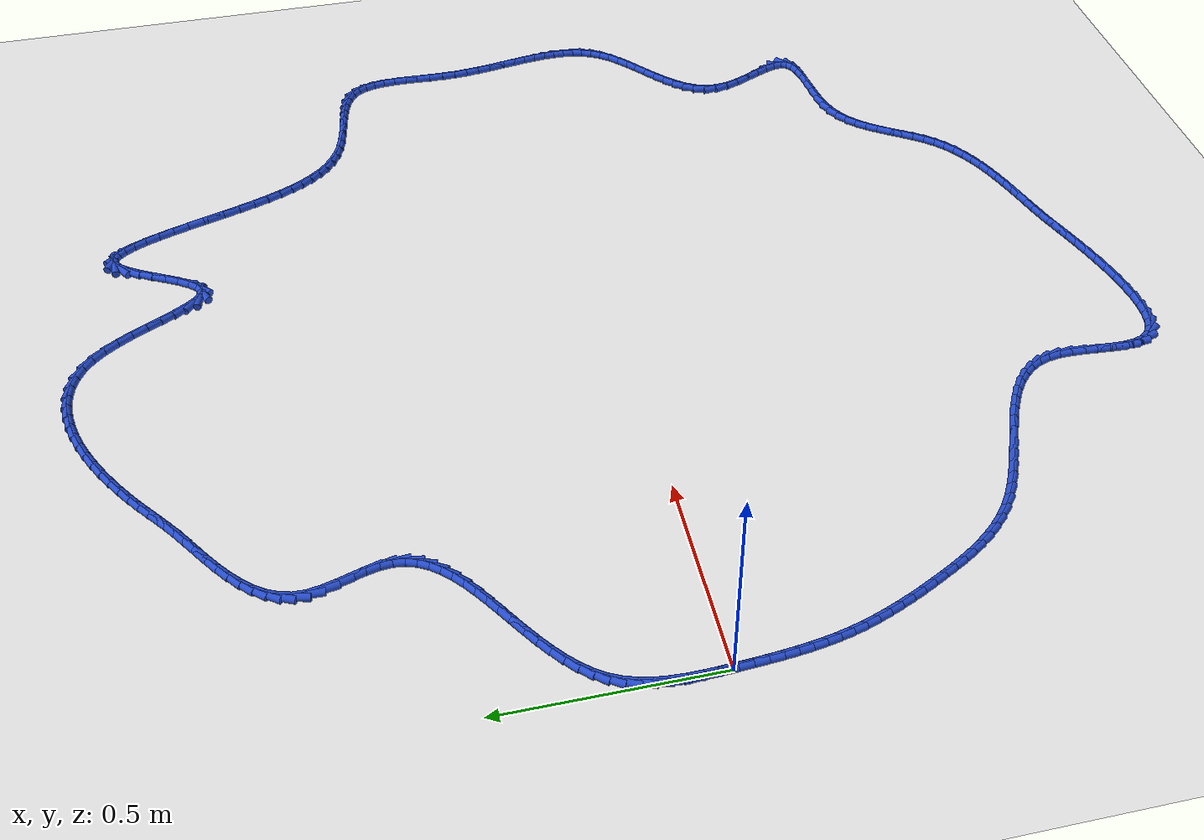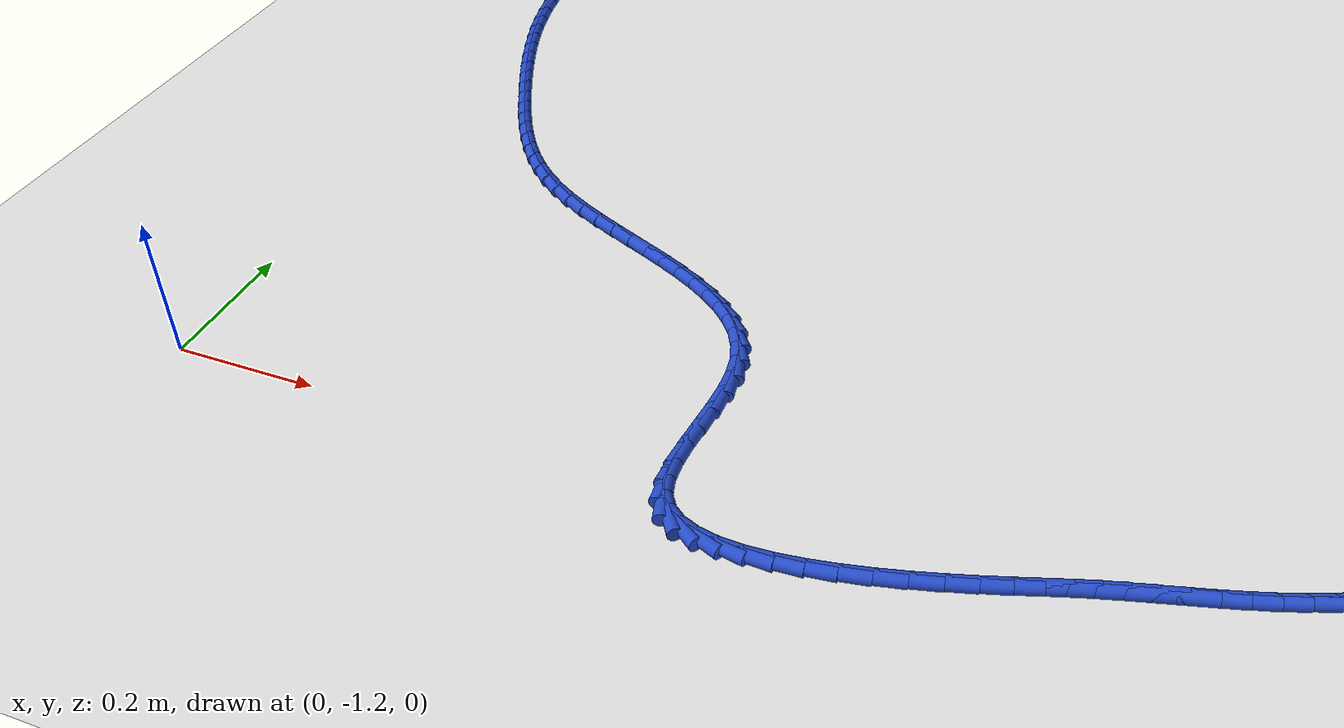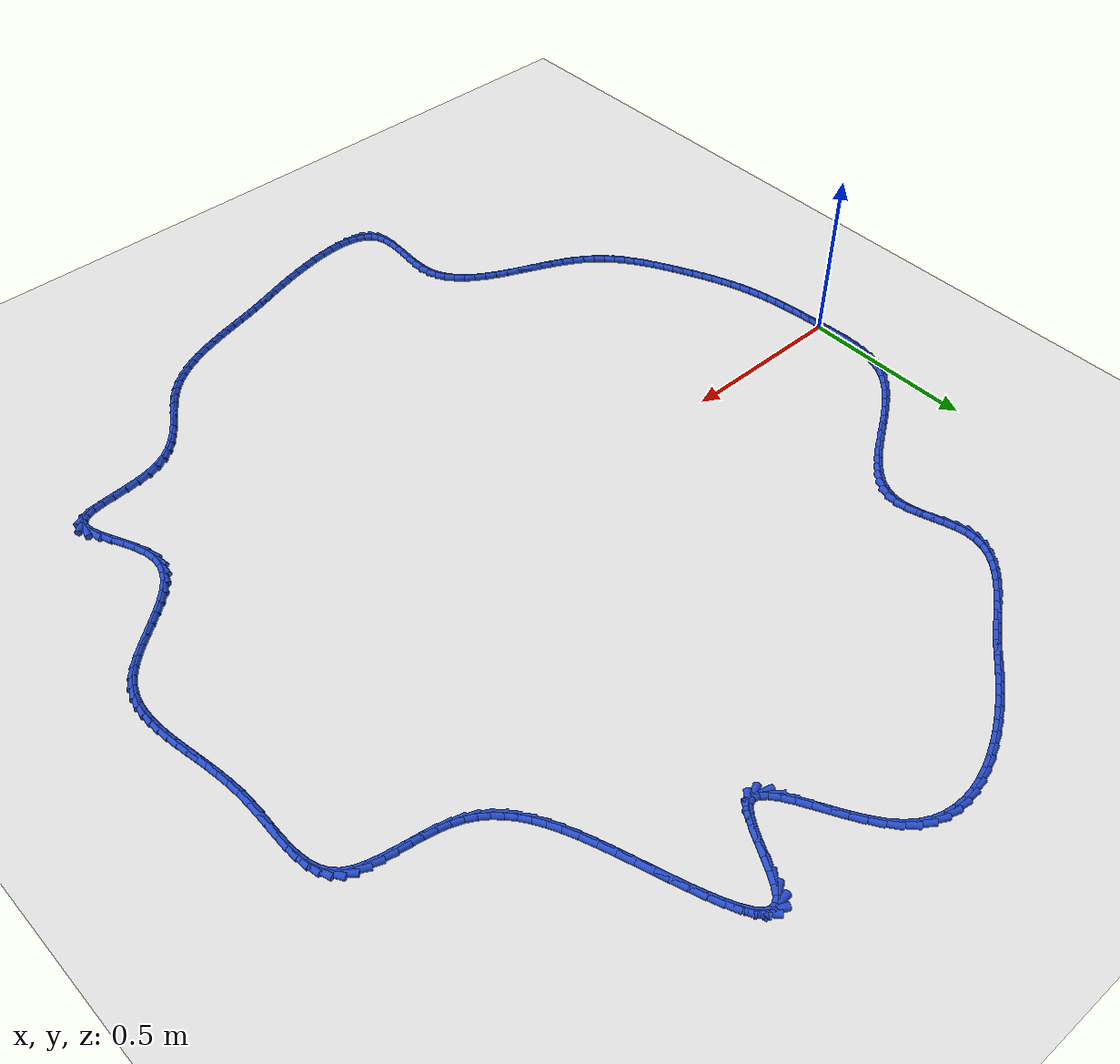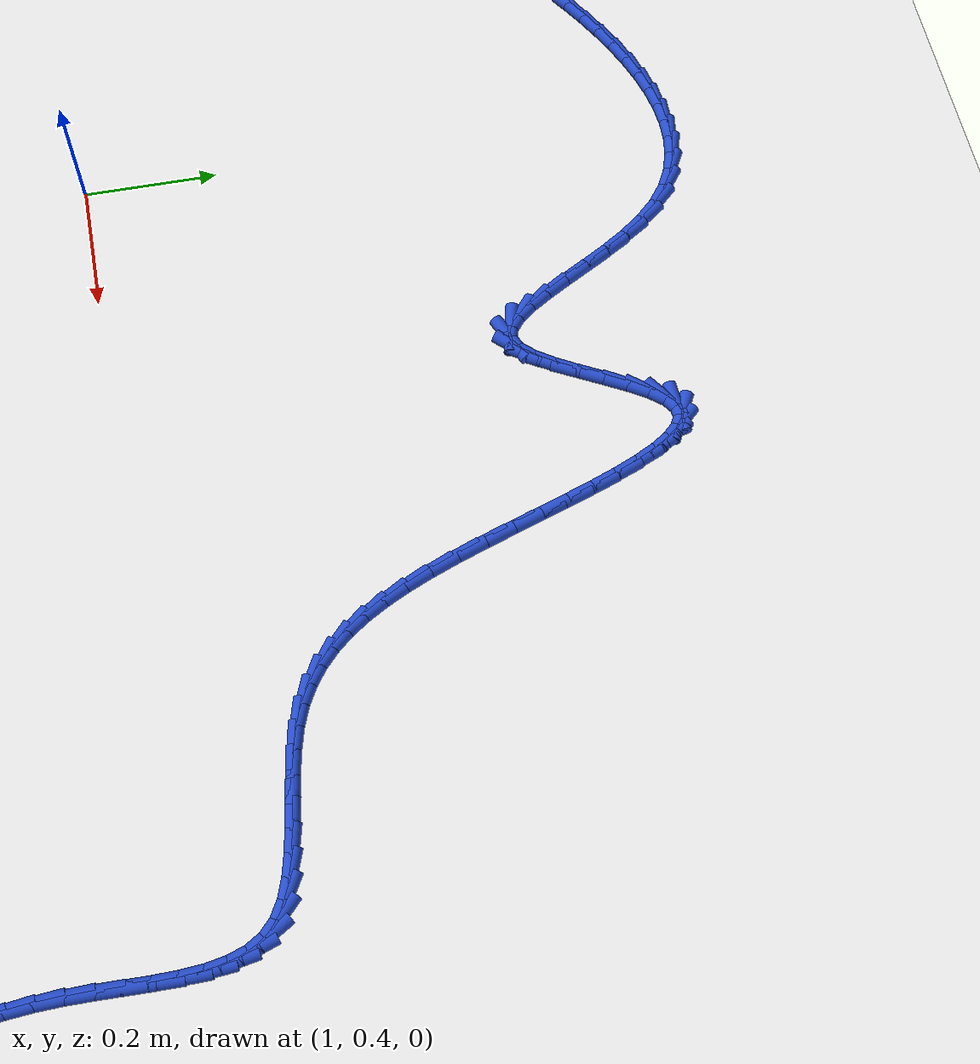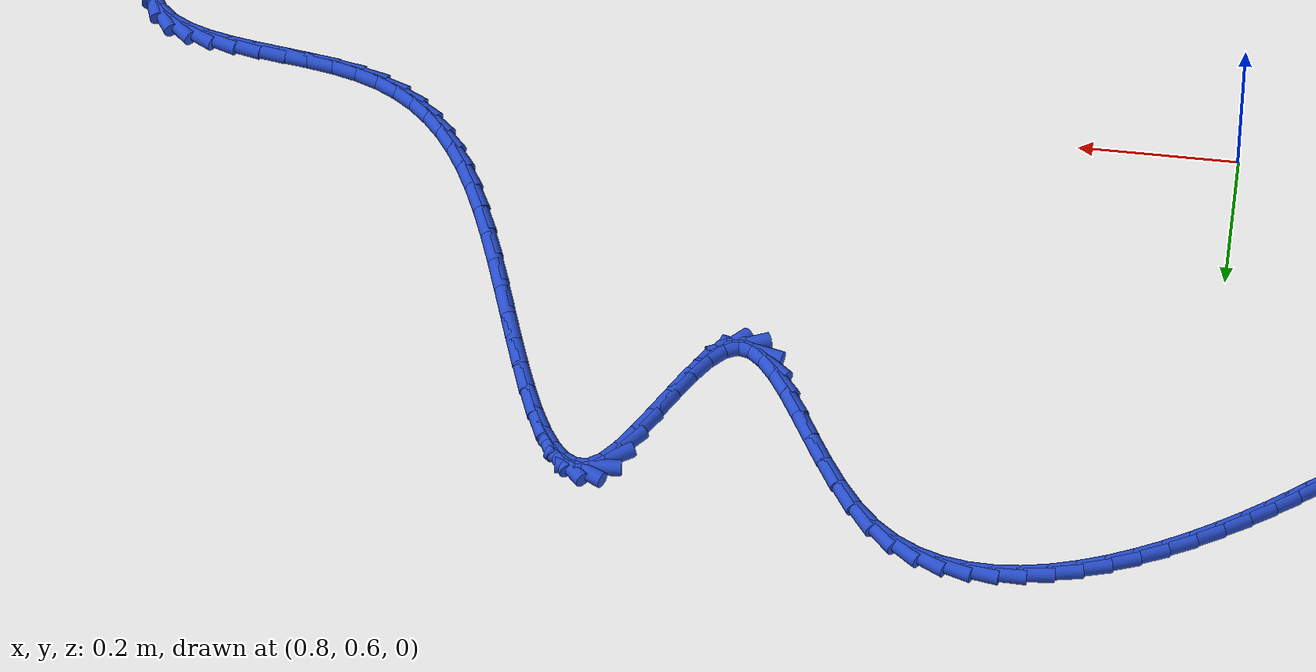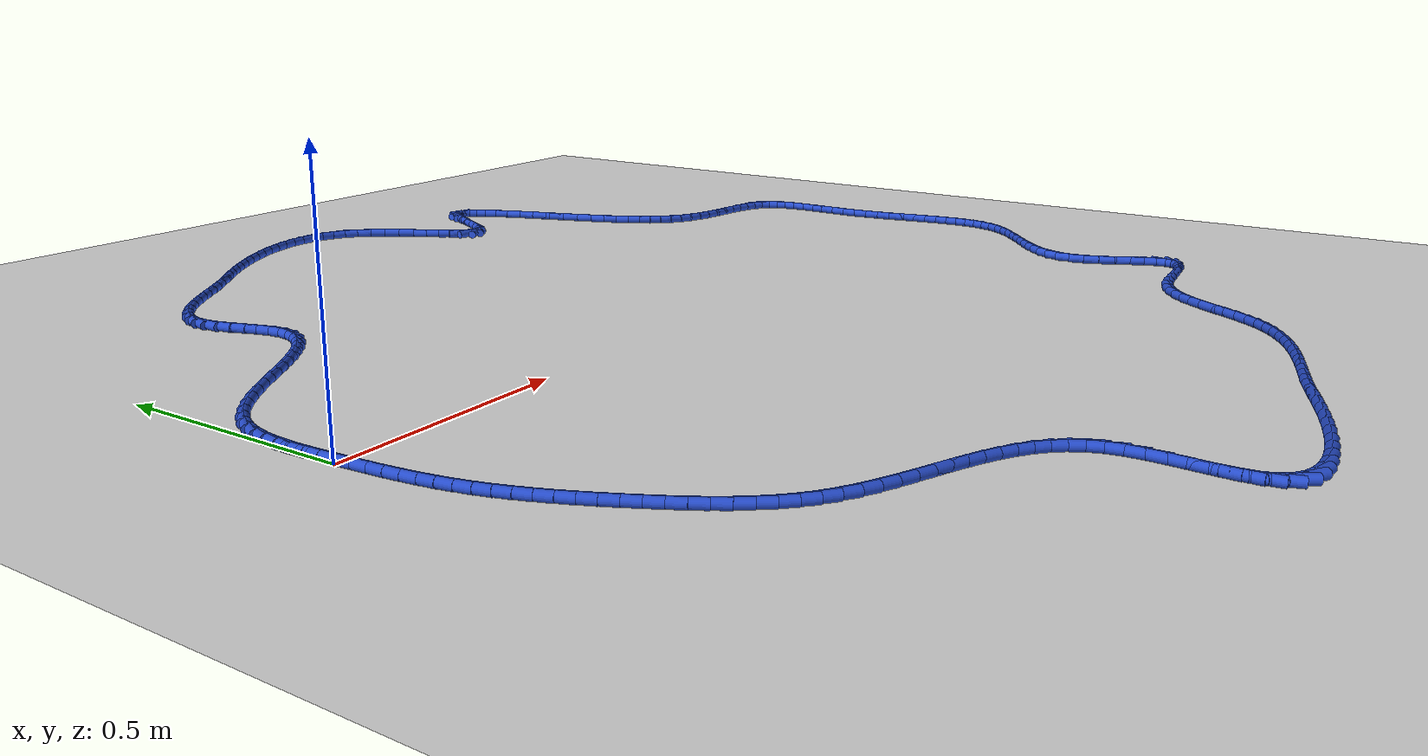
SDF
<sdf version="1.6">
 <world name="default">
  <light name="sun" type="directional">
   <pose>0 0 10 0 -0 0</pose>
   <diffuse>0.8 0.8 0.8 1</diffuse>
   <specular>0.2 0.2 0.2 1</specular>
   <attenuation>
    <range>1000</range>
    <constant>0.9</constant>
    <linear>0.01</linear>
    <quadratic>0.001</quadratic>
   </attenuation>
   <direction>-0.5 0.1 -0.9</direction>
  </light>
  <model name="ground_plane">
   <static>1</static>
   <link name="link">
    <collision name="collision">
     <geometry><plane><normal>0 0 1</normal><size>100 100</size></plane></geometry>
     <surface><friction><ode><mu>100</mu><mu2>50</mu2></ode></friction></surface>
    </collision>
    <visual name="visual">
     <cast_shadows>0</cast_shadows>
     <geometry><plane><normal>0 0 1</normal><size>100 100</size></plane></geometry>
     <material>
      <script><uri>file://media/materials/scripts/gazebo.material</uri><name>Gazebo/WhiteGlow</name></script>
     </material>
    </visual>
   </link>
  </model>
  <gravity>0 0 -9.8</gravity>
  <magnetic_field>6e-06 2.3e-05 -4.2e-05</magnetic_field>
  <atmosphere type="adiabatic"/>
  <physics name="default_physics" default="0" type="ode">
   <max_step_size>0.001</max_step_size>
   <real_time_factor>1</real_time_factor>
   <real_time_update_rate>1000</real_time_update_rate>
  </physics>
  <scene><ambient>0.4 0.4 0.4 1</ambient><background>0.7 0.7 0.7 1</background><shadows>1</shadows></scene>
  <spherical_coordinates>
   <surface_model>EARTH_WGS84</surface_model>
   <latitude_deg>0</latitude_deg>
   <longitude_deg>0</longitude_deg>
   <elevation>0</elevation>
   <heading_deg>0</heading_deg>
  </spherical_coordinates>
  <model name="line">
   <link name="link_0">
    <pose>1.3010426069826053e-17 -6.245004513516506e-17 0.01 0 1.57 -1.5148569797541769</pose>
    <collision name="collision">
     <geometry><cylinder><radius>0.01</radius><length>0.08</length></cylinder></geometry>
    </collision>
    <visual name="visual">
     <material>
      <script><name>Gazebo/Blue</name><uri>file://media/materials/scripts/gazebo.material</uri></script>
     </material>
     <geometry><cylinder><radius>0.01</radius><length>0.08</length></cylinder></geometry>
    </visual>
   </link>
   <link name="link_1">
    <pose>-0.0018274710200580691 0.03263471131374366 0.01 0 1.57 -1.5335563678883095</pose>
    <collision name="collision">
     <geometry><cylinder><radius>0.01</radius><length>0.08</length></cylinder></geometry>
    </collision>
    <visual name="visual">
     <material>
      <script><name>Gazebo/Blue</name><uri>file://media/materials/scripts/gazebo.material</uri></script>
     </material>
     <geometry><cylinder><radius>0.01</radius><length>0.08</length></cylinder></geometry>
    </visual>
   </link>
   <link name="link_2">
    <pose>-0.003047726917026739 0.06538694281670723 0.01 0 1.57 -1.5680371676612026</pose>
    <collision name="collision">
     <geometry><cylinder><radius>0.01</radius><length>0.08</length></cylinder></geometry>
    </collision>
    <visual name="visual">
     <material>
      <script><name>Gazebo/Blue</name><uri>file://media/materials/scripts/gazebo.material</uri></script>
     </material>
     <geometry><cylinder><radius>0.01</radius><length>0.08</length></cylinder></geometry>
    </visual>
   </link>
   <link name="link_3">
    <pose>-0.003137669802470727 0.09798479340882538 0.01 0 1.57 1.5222367138957367</pose>
    <collision name="collision">
     <geometry><cylinder><radius>0.01</radius><length>0.08</length></cylinder></geometry>
    </collision>
    <visual name="visual">
     <material>
      <script><name>Gazebo/Blue</name><uri>file://media/materials/scripts/gazebo.material</uri></script>
     </material>
     <geometry><cylinder><radius>0.01</radius><length>0.08</length></cylinder></geometry>
    </visual>
   </link>
   <link name="link_4">
    <pose>-0.0015742017879547708 0.13015636199003294 0.01 0 1.57 1.4525211263077098</pose>
    <collision name="collision">
     <geometry><cylinder><radius>0.01</radius><length>0.08</length></cylinder></geometry>
    </collision>
    <visual name="visual">
     <material>
      <script><name>Gazebo/Blue</name><uri>file://media/materials/scripts/gazebo.material</uri></script>
     </material>
     <geometry><cylinder><radius>0.01</radius><length>0.08</length></cylinder></geometry>
    </visual>
   </link>
   <link name="link_5">
    <pose>0.0021657750149564024 0.16162974746026446 0.01 0 1.57 1.36274026349538</pose>
    <collision name="collision">
     <geometry><cylinder><radius>0.01</radius><length>0.08</length></cylinder></geometry>
    </collision>
    <visual name="visual">
     <material>
      <script><name>Gazebo/Blue</name><uri>file://media/materials/scripts/gazebo.material</uri></script>
     </material>
     <geometry><cylinder><radius>0.01</radius><length>0.08</length></cylinder></geometry>
    </visual>
   </link>
   <link name="link_6">
    <pose>0.008605358494698057 0.1921330487194548 0.01 0 1.57 1.2518622084039916</pose>
    <collision name="collision">
     <geometry><cylinder><radius>0.01</radius><length>0.08</length></cylinder></geometry>
    </collision>
    <visual name="visual">
     <material>
      <script><name>Gazebo/Blue</name><uri>file://media/materials/scripts/gazebo.material</uri></script>
     </material>
     <geometry><cylinder><radius>0.01</radius><length>0.08</length></cylinder></geometry>
    </visual>
   </link>
   <link name="link_7">
    <pose>0.01826764653970546 0.2213943646675386 0.01 0 1.57 1.120663291773073</pose>
    <collision name="collision">
     <geometry><cylinder><radius>0.01</radius><length>0.08</length></cylinder></geometry>
    </collision>
    <visual name="visual">
     <material>
      <script><name>Gazebo/Blue</name><uri>file://media/materials/scripts/gazebo.material</uri></script>
     </material>
     <geometry><cylinder><radius>0.01</radius><length>0.08</length></cylinder></geometry>
    </visual>
   </link>
   <link name="link_8">
    <pose>0.03167573614848738 0.24914179458922858 0.01 0 1.57 0.9797533914952946</pose>
    <collision name="collision">
     <geometry><cylinder><radius>0.01</radius><length>0.08</length></cylinder></geometry>
    </collision>
    <visual name="visual">
     <material>
      <script><name>Gazebo/Blue</name><uri>file://media/materials/scripts/gazebo.material</uri></script>
     </material>
     <geometry><cylinder><radius>0.01</radius><length>0.08</length></cylinder></geometry>
    </visual>
   </link>
   <link name="link_9">
    <pose>0.04915508737104207 0.2751888901492586 0.01 0 1.57 0.8589554902826203</pose>
    <collision name="collision">
     <geometry><cylinder><radius>0.01</radius><length>0.08</length></cylinder></geometry>
    </collision>
    <visual name="visual">
     <material>
      <script><name>Gazebo/Blue</name><uri>file://media/materials/scripts/gazebo.material</uri></script>
     </material>
     <geometry><cylinder><radius>0.01</radius><length>0.08</length></cylinder></geometry>
    </visual>
   </link>
   <link name="link_10">
    <pose>0.07027943407966906 0.2996742272120006 0.01 0 1.57 0.7637339579101653</pose>
    <collision name="collision">
     <geometry><cylinder><radius>0.01</radius><length>0.08</length></cylinder></geometry>
    </collision>
    <visual name="visual">
     <material>
      <script><name>Gazebo/Blue</name><uri>file://media/materials/scripts/gazebo.material</uri></script>
     </material>
     <geometry><cylinder><radius>0.01</radius><length>0.08</length></cylinder></geometry>
    </visual>
   </link>
   <link name="link_11">
    <pose>0.0944438118780425 0.3228136454959529 0.01 0 1.57 0.6912478016528538</pose>
    <collision name="collision">
     <geometry><cylinder><radius>0.01</radius><length>0.08</length></cylinder></geometry>
    </collision>
    <visual name="visual">
     <material>
      <script><name>Gazebo/Blue</name><uri>file://media/materials/scripts/gazebo.material</uri></script>
     </material>
     <geometry><cylinder><radius>0.01</radius><length>0.08</length></cylinder></geometry>
    </visual>
   </link>
   <link name="link_12">
    <pose>0.12104325636983655 0.3448229847196139 0.01 0 1.57 0.6383699507317454</pose>
    <collision name="collision">
     <geometry><cylinder><radius>0.01</radius><length>0.08</length></cylinder></geometry>
    </collision>
    <visual name="visual">
     <material>
      <script><name>Gazebo/Blue</name><uri>file://media/materials/scripts/gazebo.material</uri></script>
     </material>
     <geometry><cylinder><radius>0.01</radius><length>0.08</length></cylinder></geometry>
    </visual>
   </link>
   <link name="link_13">
    <pose>0.14947280315872527 0.36591808460148223 0.01 0 1.57 0.6024957956063791</pose>
    <collision name="collision">
     <geometry><cylinder><radius>0.01</radius><length>0.08</length></cylinder></geometry>
    </collision>
    <visual name="visual">
     <material>
      <script><name>Gazebo/Blue</name><uri>file://media/materials/scripts/gazebo.material</uri></script>
     </material>
     <geometry><cylinder><radius>0.01</radius><length>0.08</length></cylinder></geometry>
    </visual>
   </link>
   <link name="link_14">
    <pose>0.17912748784838273 0.38631478486005605 0.01 0 1.57 0.5818237485095887</pose>
    <collision name="collision">
     <geometry><cylinder><radius>0.01</radius><length>0.08</length></cylinder></geometry>
    </collision>
    <visual name="visual">
     <material>
      <script><name>Gazebo/Blue</name><uri>file://media/materials/scripts/gazebo.material</uri></script>
     </material>
     <geometry><cylinder><radius>0.01</radius><length>0.08</length></cylinder></geometry>
    </visual>
   </link>
   <link name="link_15">
    <pose>0.20940234604248303 0.4062289252138337 0.01 0 1.57 0.5754202109277422</pose>
    <collision name="collision">
     <geometry><cylinder><radius>0.01</radius><length>0.08</length></cylinder></geometry>
    </collision>
    <visual name="visual">
     <material>
      <script><name>Gazebo/Blue</name><uri>file://media/materials/scripts/gazebo.material</uri></script>
     </material>
     <geometry><cylinder><radius>0.01</radius><length>0.08</length></cylinder></geometry>
    </visual>
   </link>
   <link name="link_16">
    <pose>0.23969241334470043 0.42587634538131386 0.01 0 1.57 0.5832401030725402</pose>
    <collision name="collision">
     <geometry><cylinder><radius>0.01</radius><length>0.08</length></cylinder></geometry>
    </collision>
    <visual name="visual">
     <material>
      <script><name>Gazebo/Blue</name><uri>file://media/materials/scripts/gazebo.material</uri></script>
     </material>
     <geometry><cylinder><radius>0.01</radius><length>0.08</length></cylinder></geometry>
    </visual>
   </link>
   <link name="link_17">
    <pose>0.26939272535870895 0.44547288508099475 0.01 0 1.57 0.6061813132550719</pose>
    <collision name="collision">
     <geometry><cylinder><radius>0.01</radius><length>0.08</length></cylinder></geometry>
    </collision>
    <visual name="visual">
     <material>
      <script><name>Gazebo/Blue</name><uri>file://media/materials/scripts/gazebo.material</uri></script>
     </material>
     <geometry><cylinder><radius>0.01</radius><length>0.08</length></cylinder></geometry>
    </visual>
   </link>
   <link name="link_18">
    <pose>0.29789831768818276 0.4652343840313748 0.01 0 1.57 0.646200447591836</pose>
    <collision name="collision">
     <geometry><cylinder><radius>0.01</radius><length>0.08</length></cylinder></geometry>
    </collision>
    <visual name="visual">
     <material>
      <script><name>Gazebo/Blue</name><uri>file://media/materials/scripts/gazebo.material</uri></script>
     </material>
     <geometry><cylinder><radius>0.01</radius><length>0.08</length></cylinder></geometry>
    </visual>
   </link>
   <link name="link_19">
    <pose>0.3246042259367956 0.4853766819509522 0.01 0 1.57 0.7064703811190257</pose>
    <collision name="collision">
     <geometry><cylinder><radius>0.01</radius><length>0.08</length></cylinder></geometry>
    </collision>
    <visual name="visual">
     <material>
      <script><name>Gazebo/Blue</name><uri>file://media/materials/scripts/gazebo.material</uri></script>
     </material>
     <geometry><cylinder><radius>0.01</radius><length>0.08</length></cylinder></geometry>
    </visual>
   </link>
   <link name="link_20">
    <pose>0.3489054857082222 0.5061156185582257 0.01 0 1.57 0.7914613372405801</pose>
    <collision name="collision">
     <geometry><cylinder><radius>0.01</radius><length>0.08</length></cylinder></geometry>
    </collision>
    <visual name="visual">
     <material>
      <script><name>Gazebo/Blue</name><uri>file://media/materials/scripts/gazebo.material</uri></script>
     </material>
     <geometry><cylinder><radius>0.01</radius><length>0.08</length></cylinder></geometry>
    </visual>
   </link>
   <link name="link_21">
    <pose>0.3701971326061363 0.5276670335716935 0.01 0 1.57 0.9065861024835763</pose>
    <collision name="collision">
     <geometry><cylinder><radius>0.01</radius><length>0.08</length></cylinder></geometry>
    </collision>
    <visual name="visual">
     <material>
      <script><name>Gazebo/Blue</name><uri>file://media/materials/scripts/gazebo.material</uri></script>
     </material>
     <geometry><cylinder><radius>0.01</radius><length>0.08</length></cylinder></geometry>
    </visual>
   </link>
   <link name="link_22">
    <pose>0.38787420223421204 0.5502467667098541 0.01 0 1.57 1.0566043031465027</pose>
    <collision name="collision">
     <geometry><cylinder><radius>0.01</radius><length>0.08</length></cylinder></geometry>
    </collision>
    <visual name="visual">
     <material>
      <script><name>Gazebo/Blue</name><uri>file://media/materials/scripts/gazebo.material</uri></script>
     </material>
     <geometry><cylinder><radius>0.01</radius><length>0.08</length></cylinder></geometry>
    </visual>
   </link>
   <link name="link_23">
    <pose>0.40133173019612356 0.5740706576912057 0.01 0 1.57 1.2417643785597179</pose>
    <collision name="collision">
     <geometry><cylinder><radius>0.01</radius><length>0.08</length></cylinder></geometry>
    </collision>
    <visual name="visual">
     <material>
      <script><name>Gazebo/Blue</name><uri>file://media/materials/scripts/gazebo.material</uri></script>
     </material>
     <geometry><cylinder><radius>0.01</radius><length>0.08</length></cylinder></geometry>
    </visual>
   </link>
   <link name="link_24">
    <pose>0.4099647520955449 0.5993545462342467 0.01 0 1.57 1.4525236130481365</pose>
    <collision name="collision">
     <geometry><cylinder><radius>0.01</radius><length>0.08</length></cylinder></geometry>
    </collision>
    <visual name="visual">
     <material>
      <script><name>Gazebo/Blue</name><uri>file://media/materials/scripts/gazebo.material</uri></script>
     </material>
     <geometry><cylinder><radius>0.01</radius><length>0.08</length></cylinder></geometry>
    </visual>
   </link>
   <link name="link_25">
    <pose>0.41316830353615036 0.6263142720574757 0.01 0 1.57 -1.4799108557381302</pose>
    <collision name="collision">
     <geometry><cylinder><radius>0.01</radius><length>0.08</length></cylinder></geometry>
    </collision>
    <visual name="visual">
     <material>
      <script><name>Gazebo/Blue</name><uri>file://media/materials/scripts/gazebo.material</uri></script>
     </material>
     <geometry><cylinder><radius>0.01</radius><length>0.08</length></cylinder></geometry>
    </visual>
   </link>
   <link name="link_26">
    <pose>0.4105444815305706 0.6551042820495876 0.01 0 1.57 -1.337546073702736</pose>
    <collision name="collision">
     <geometry><cylinder><radius>0.01</radius><length>0.08</length></cylinder></geometry>
    </collision>
    <visual name="visual">
     <material>
      <script><name>Gazebo/Blue</name><uri>file://media/materials/scripts/gazebo.material</uri></script>
     </material>
     <geometry><cylinder><radius>0.01</radius><length>0.08</length></cylinder></geometry>
    </visual>
   </link>
   <link name="link_27">
    <pose>0.4033497213102262 0.6853885188318901 0.01 0 1.57 -1.2689618991153977</pose>
    <collision name="collision">
     <geometry><cylinder><radius>0.01</radius><length>0.08</length></cylinder></geometry>
    </collision>
    <visual name="visual">
     <material>
      <script><name>Gazebo/Blue</name><uri>file://media/materials/scripts/gazebo.material</uri></script>
     </material>
     <geometry><cylinder><radius>0.01</radius><length>0.08</length></cylinder></geometry>
    </visual>
   </link>
   <link name="link_28">
    <pose>0.3936334113282727 0.716595817757613 0.01 0 1.57 -1.2586515629719093</pose>
    <collision name="collision">
     <geometry><cylinder><radius>0.01</radius><length>0.08</length></cylinder></geometry>
    </collision>
    <visual name="visual">
     <material>
      <script><name>Gazebo/Blue</name><uri>file://media/materials/scripts/gazebo.material</uri></script>
     </material>
     <geometry><cylinder><radius>0.01</radius><length>0.08</length></cylinder></geometry>
    </visual>
   </link>
   <link name="link_29">
    <pose>0.38344992591930827 0.748153535887279 0.01 0 1.57 -1.3030525129866226</pose>
    <collision name="collision">
     <geometry><cylinder><radius>0.01</radius><length>0.08</length></cylinder></geometry>
    </collision>
    <visual name="visual">
     <material>
      <script><name>Gazebo/Blue</name><uri>file://media/materials/scripts/gazebo.material</uri></script>
     </material>
     <geometry><cylinder><radius>0.01</radius><length>0.08</length></cylinder></geometry>
    </visual>
   </link>
   <link name="link_30">
    <pose>0.37485363941793093 0.7794890302814096 0.01 0 1.57 -1.4099640663923607</pose>
    <collision name="collision">
     <geometry><cylinder><radius>0.01</radius><length>0.08</length></cylinder></geometry>
    </collision>
    <visual name="visual">
     <material>
      <script><name>Gazebo/Blue</name><uri>file://media/materials/scripts/gazebo.material</uri></script>
     </material>
     <geometry><cylinder><radius>0.01</radius><length>0.08</length></cylinder></geometry>
    </visual>
   </link>
   <link name="link_31">
    <pose>0.36989892615873876 0.8100296580005276 0.01 0 1.57 1.547256196846472</pose>
    <collision name="collision">
     <geometry><cylinder><radius>0.01</radius><length>0.08</length></cylinder></geometry>
    </collision>
    <visual name="visual">
     <material>
      <script><name>Gazebo/Blue</name><uri>file://media/materials/scripts/gazebo.material</uri></script>
     </material>
     <geometry><cylinder><radius>0.01</radius><length>0.08</length></cylinder></geometry>
    </visual>
   </link>
   <link name="link_32">
    <pose>0.37058610890254545 0.8392162346817138 0.01 0 1.57 1.3230002201486062</pose>
    <collision name="collision">
     <geometry><cylinder><radius>0.01</radius><length>0.08</length></cylinder></geometry>
    </collision>
    <visual name="visual">
     <material>
      <script><name>Gazebo/Blue</name><uri>file://media/materials/scripts/gazebo.material</uri></script>
     </material>
     <geometry><cylinder><radius>0.01</radius><length>0.08</length></cylinder></geometry>
    </visual>
   </link>
   <link name="link_33">
    <pose>0.37757085197509865 0.8668243893120926 0.01 0 1.57 1.1238958005347761</pose>
    <collision name="collision">
     <geometry><cylinder><radius>0.01</radius><length>0.08</length></cylinder></geometry>
    </collision>
    <visual name="visual">
     <material>
      <script><name>Gazebo/Blue</name><uri>file://media/materials/scripts/gazebo.material</uri></script>
     </material>
     <geometry><cylinder><radius>0.01</radius><length>0.08</length></cylinder></geometry>
    </visual>
   </link>
   <link name="link_34">
    <pose>0.3901052485337616 0.8929792332102517 0.01 0 1.57 0.9633147970958522</pose>
    <collision name="collision">
     <geometry><cylinder><radius>0.01</radius><length>0.08</length></cylinder></geometry>
    </collision>
    <visual name="visual">
     <material>
      <script><name>Gazebo/Blue</name><uri>file://media/materials/scripts/gazebo.material</uri></script>
     </material>
     <geometry><cylinder><radius>0.01</radius><length>0.08</length></cylinder></geometry>
    </visual>
   </link>
   <link name="link_35">
    <pose>0.4073755508236865 0.9178222717587395 0.01 0 1.57 0.8406248482329952</pose>
    <collision name="collision">
     <geometry><cylinder><radius>0.01</radius><length>0.08</length></cylinder></geometry>
    </collision>
    <visual name="visual">
     <material>
      <script><name>Gazebo/Blue</name><uri>file://media/materials/scripts/gazebo.material</uri></script>
     </material>
     <geometry><cylinder><radius>0.01</radius><length>0.08</length></cylinder></geometry>
    </visual>
   </link>
   <link name="link_36">
    <pose>0.4285680110900251 0.9414950103401034 0.01 0 1.57 0.7501176114586856</pose>
    <collision name="collision">
     <geometry><cylinder><radius>0.01</radius><length>0.08</length></cylinder></geometry>
    </collision>
    <visual name="visual">
     <material>
      <script><name>Gazebo/Blue</name><uri>file://media/materials/scripts/gazebo.material</uri></script>
     </material>
     <geometry><cylinder><radius>0.01</radius><length>0.08</length></cylinder></geometry>
    </visual>
   </link>
   <link name="link_37">
    <pose>0.45286888157792937 0.9641389543368902 0.01 0 1.57 0.6856545789041404</pose>
    <collision name="collision">
     <geometry><cylinder><radius>0.01</radius><length>0.08</length></cylinder></geometry>
    </collision>
    <visual name="visual">
     <material>
      <script><name>Gazebo/Blue</name><uri>file://media/materials/scripts/gazebo.material</uri></script>
     </material>
     <geometry><cylinder><radius>0.01</radius><length>0.08</length></cylinder></geometry>
    </visual>
   </link>
   <link name="link_38">
    <pose>0.4794644145325515 0.9858956091316484 0.01 0 1.57 0.6424411069628106</pose>
    <collision name="collision">
     <geometry><cylinder><radius>0.01</radius><length>0.08</length></cylinder></geometry>
    </collision>
    <visual name="visual">
     <material>
      <script><name>Gazebo/Blue</name><uri>file://media/materials/scripts/gazebo.material</uri></script>
     </material>
     <geometry><cylinder><radius>0.01</radius><length>0.08</length></cylinder></geometry>
    </visual>
   </link>
   <link name="link_39">
    <pose>0.5075408621990434 1.0069064801069247 0.01 0 1.57 0.6173741135556308</pose>
    <collision name="collision">
     <geometry><cylinder><radius>0.01</radius><length>0.08</length></cylinder></geometry>
    </collision>
    <visual name="visual">
     <material>
      <script><name>Gazebo/Blue</name><uri>file://media/materials/scripts/gazebo.material</uri></script>
     </material>
     <geometry><cylinder><radius>0.01</radius><length>0.08</length></cylinder></geometry>
    </visual>
   </link>
   <link name="link_40">
    <pose>0.536284476822557 1.027313072645267 0.01 0 1.57 0.6089847023817875</pose>
    <collision name="collision">
     <geometry><cylinder><radius>0.01</radius><length>0.08</length></cylinder></geometry>
    </collision>
    <visual name="visual">
     <material>
      <script><name>Gazebo/Blue</name><uri>file://media/materials/scripts/gazebo.material</uri></script>
     </material>
     <geometry><cylinder><radius>0.01</radius><length>0.08</length></cylinder></geometry>
    </visual>
   </link>
   <link name="link_41">
    <pose>0.5648815106482443 1.047256892129223 0.01 0 1.57 0.6174177051610813</pose>
    <collision name="collision">
     <geometry><cylinder><radius>0.01</radius><length>0.08</length></cylinder></geometry>
    </collision>
    <visual name="visual">
     <material>
      <script><name>Gazebo/Blue</name><uri>file://media/materials/scripts/gazebo.material</uri></script>
     </material>
     <geometry><cylinder><radius>0.01</radius><length>0.08</length></cylinder></geometry>
    </visual>
   </link>
   <link name="link_42">
    <pose>0.5925182159212574 1.0668794439413396 0.01 0 1.57 0.6433077660875999</pose>
    <collision name="collision">
     <geometry><cylinder><radius>0.01</radius><length>0.08</length></cylinder></geometry>
    </collision>
    <visual name="visual">
     <material>
      <script><name>Gazebo/Blue</name><uri>file://media/materials/scripts/gazebo.material</uri></script>
     </material>
     <geometry><cylinder><radius>0.01</radius><length>0.08</length></cylinder></geometry>
    </visual>
   </link>
   <link name="link_43">
    <pose>0.618450711420147 1.0863209825468068 0.01 0 1.57 0.670118501557556</pose>
    <collision name="collision">
     <geometry><cylinder><radius>0.01</radius><length>0.08</length></cylinder></geometry>
    </collision>
    <visual name="visual">
     <material>
      <script><name>Gazebo/Blue</name><uri>file://media/materials/scripts/gazebo.material</uri></script>
     </material>
     <geometry><cylinder><radius>0.01</radius><length>0.08</length></cylinder></geometry>
    </visual>
   </link>
   <link name="link_44">
    <pose>0.6429107817587572 1.1057042937134305 0.01 0 1.57 0.6819829245997432</pose>
    <collision name="collision">
     <geometry><cylinder><radius>0.01</radius><length>0.08</length></cylinder></geometry>
    </collision>
    <visual name="visual">
     <material>
      <script><name>Gazebo/Blue</name><uri>file://media/materials/scripts/gazebo.material</uri></script>
     </material>
     <geometry><cylinder><radius>0.01</radius><length>0.08</length></cylinder></geometry>
    </visual>
   </link>
   <link name="link_45">
    <pose>0.6668471357826383 1.1251393271210899 0.01 0 1.57 0.6770895313294641</pose>
    <collision name="collision">
     <geometry><cylinder><radius>0.01</radius><length>0.08</length></cylinder></geometry>
    </collision>
    <visual name="visual">
     <material>
      <script><name>Gazebo/Blue</name><uri>file://media/materials/scripts/gazebo.material</uri></script>
     </material>
     <geometry><cylinder><radius>0.01</radius><length>0.08</length></cylinder></geometry>
    </visual>
   </link>
   <link name="link_46">
    <pose>0.6912250552602538 1.1447357357216605 0.01 0 1.57 0.6566315655434309</pose>
    <collision name="collision">
     <geometry><cylinder><radius>0.01</radius><length>0.08</length></cylinder></geometry>
    </collision>
    <visual name="visual">
     <material>
      <script><name>Gazebo/Blue</name><uri>file://media/materials/scripts/gazebo.material</uri></script>
     </material>
     <geometry><cylinder><radius>0.01</radius><length>0.08</length></cylinder></geometry>
    </visual>
   </link>
   <link name="link_47">
    <pose>0.7169939945971804 1.1645964136851985 0.01 0 1.57 0.627439123160565</pose>
    <collision name="collision">
     <geometry><cylinder><radius>0.01</radius><length>0.08</length></cylinder></geometry>
    </collision>
    <visual name="visual">
     <material>
      <script><name>Gazebo/Blue</name><uri>file://media/materials/scripts/gazebo.material</uri></script>
     </material>
     <geometry><cylinder><radius>0.01</radius><length>0.08</length></cylinder></geometry>
    </visual>
   </link>
   <link name="link_48">
    <pose>0.7445765286283277 1.1845992610315113 0.01 0 1.57 0.5950037742382264</pose>
    <collision name="collision">
     <geometry><cylinder><radius>0.01</radius><length>0.08</length></cylinder></geometry>
    </collision>
    <visual name="visual">
     <material>
      <script><name>Gazebo/Blue</name><uri>file://media/materials/scripts/gazebo.material</uri></script>
     </material>
     <geometry><cylinder><radius>0.01</radius><length>0.08</length></cylinder></geometry>
    </visual>
   </link>
   <link name="link_49">
    <pose>0.7737579565509702 1.2043500410369339 0.01 0 1.57 0.5587999099870883</pose>
    <collision name="collision">
     <geometry><cylinder><radius>0.01</radius><length>0.08</length></cylinder></geometry>
    </collision>
    <visual name="visual">
     <material>
      <script><name>Gazebo/Blue</name><uri>file://media/materials/scripts/gazebo.material</uri></script>
     </material>
     <geometry><cylinder><radius>0.01</radius><length>0.08</length></cylinder></geometry>
    </visual>
   </link>
   <link name="link_50">
    <pose>0.8042854202178796 1.2234382225914175 0.01 0 1.57 0.5178605148760809</pose>
    <collision name="collision">
     <geometry><cylinder><radius>0.01</radius><length>0.08</length></cylinder></geometry>
    </collision>
    <visual name="visual">
     <material>
      <script><name>Gazebo/Blue</name><uri>file://media/materials/scripts/gazebo.material</uri></script>
     </material>
     <geometry><cylinder><radius>0.01</radius><length>0.08</length></cylinder></geometry>
    </visual>
   </link>
   <link name="link_51">
    <pose>0.8359060614818283 1.241453274584913 0.01 0 1.57 0.4710360252592495</pose>
    <collision name="collision">
     <geometry><cylinder><radius>0.01</radius><length>0.08</length></cylinder></geometry>
    </collision>
    <visual name="visual">
     <material>
      <script><name>Gazebo/Blue</name><uri>file://media/materials/scripts/gazebo.material</uri></script>
     </material>
     <geometry><cylinder><radius>0.01</radius><length>0.08</length></cylinder></geometry>
    </visual>
   </link>
   <link name="link_52">
    <pose>0.8683670221955878 1.2579846659073712 0.01 0 1.57 0.4169352515023136</pose>
    <collision name="collision">
     <geometry><cylinder><radius>0.01</radius><length>0.08</length></cylinder></geometry>
    </collision>
    <visual name="visual">
     <material>
      <script><name>Gazebo/Blue</name><uri>file://media/materials/scripts/gazebo.material</uri></script>
     </material>
     <geometry><cylinder><radius>0.01</radius><length>0.08</length></cylinder></geometry>
    </visual>
   </link>
   <link name="link_53">
    <pose>0.9014154442119305 1.2726218654487447 0.01 0 1.57 0.35387281322087755</pose>
    <collision name="collision">
     <geometry><cylinder><radius>0.01</radius><length>0.08</length></cylinder></geometry>
    </collision>
    <visual name="visual">
     <material>
      <script><name>Gazebo/Blue</name><uri>file://media/materials/scripts/gazebo.material</uri></script>
     </material>
     <geometry><cylinder><radius>0.01</radius><length>0.08</length></cylinder></geometry>
    </visual>
   </link>
   <link name="link_54">
    <pose>0.9347984693836288 1.2849543420989837 0.01 0 1.57 0.2798422098387656</pose>
    <collision name="collision">
     <geometry><cylinder><radius>0.01</radius><length>0.08</length></cylinder></geometry>
    </collision>
    <visual name="visual">
     <material>
      <script><name>Gazebo/Blue</name><uri>file://media/materials/scripts/gazebo.material</uri></script>
     </material>
     <geometry><cylinder><radius>0.01</radius><length>0.08</length></cylinder></geometry>
    </visual>
   </link>
   <link name="link_55">
    <pose>0.9682632395634543 1.2945715647480396 0.01 0 1.57 0.1925593886473168</pose>
    <collision name="collision">
     <geometry><cylinder><radius>0.01</radius><length>0.08</length></cylinder></geometry>
    </collision>
    <visual name="visual">
     <material>
      <script><name>Gazebo/Blue</name><uri>file://media/materials/scripts/gazebo.material</uri></script>
     </material>
     <geometry><cylinder><radius>0.01</radius><length>0.08</length></cylinder></geometry>
    </visual>
   </link>
   <link name="link_56">
    <pose>1.001556896604179 1.3010630022858636 0.01 0 1.57 0.08966309829257738</pose>
    <collision name="collision">
     <geometry><cylinder><radius>0.01</radius><length>0.08</length></cylinder></geometry>
    </collision>
    <visual name="visual">
     <material>
      <script><name>Gazebo/Blue</name><uri>file://media/materials/scripts/gazebo.material</uri></script>
     </material>
     <geometry><cylinder><radius>0.01</radius><length>0.08</length></cylinder></geometry>
    </visual>
   </link>
   <link name="link_57">
    <pose>1.0344265823585757 1.3040181236024073 0.01 0 1.57 -0.030796039616162993</pose>
    <collision name="collision">
     <geometry><cylinder><radius>0.01</radius><length>0.08</length></cylinder></geometry>
    </collision>
    <visual name="visual">
     <material>
      <script><name>Gazebo/Blue</name><uri>file://media/materials/scripts/gazebo.material</uri></script>
     </material>
     <geometry><cylinder><radius>0.01</radius><length>0.08</length></cylinder></geometry>
    </visual>
   </link>
   <link name="link_58">
    <pose>1.0666194386794157 1.303026397587622 0.01 0 1.57 -0.16945832840128605</pose>
    <collision name="collision">
     <geometry><cylinder><radius>0.01</radius><length>0.08</length></cylinder></geometry>
    </collision>
    <visual name="visual">
     <material>
      <script><name>Gazebo/Blue</name><uri>file://media/materials/scripts/gazebo.material</uri></script>
     </material>
     <geometry><cylinder><radius>0.01</radius><length>0.08</length></cylinder></geometry>
    </visual>
   </link>
   <link name="link_59">
    <pose>1.0978826074194714 1.2976772931314584 0.01 0 1.57 -0.3244450678076632</pose>
    <collision name="collision">
     <geometry><cylinder><radius>0.01</radius><length>0.08</length></cylinder></geometry>
    </collision>
    <visual name="visual">
     <material>
      <script><name>Gazebo/Blue</name><uri>file://media/materials/scripts/gazebo.material</uri></script>
     </material>
     <geometry><cylinder><radius>0.01</radius><length>0.08</length></cylinder></geometry>
    </visual>
   </link>
   <link name="link_60">
    <pose>1.1279632304315148 1.2875602791238683 0.01 0 1.57 -0.4904465407645844</pose>
    <collision name="collision">
     <geometry><cylinder><radius>0.01</radius><length>0.08</length></cylinder></geometry>
    </collision>
    <visual name="visual">
     <material>
      <script><name>Gazebo/Blue</name><uri>file://media/materials/scripts/gazebo.material</uri></script>
     </material>
     <geometry><cylinder><radius>0.01</radius><length>0.08</length></cylinder></geometry>
    </visual>
   </link>
   <link name="link_61">
    <pose>1.156608449568318 1.2722648244548023 0.01 0 1.57 -0.6591428239276981</pose>
    <collision name="collision">
     <geometry><cylinder><radius>0.01</radius><length>0.08</length></cylinder></geometry>
    </collision>
    <visual name="visual">
     <material>
      <script><name>Gazebo/Blue</name><uri>file://media/materials/scripts/gazebo.material</uri></script>
     </material>
     <geometry><cylinder><radius>0.01</radius><length>0.08</length></cylinder></geometry>
    </visual>
   </link>
   <link name="link_62">
    <pose>1.1835654066826533 1.251380398014212 0.01 0 1.57 -0.8179534055845642</pose>
    <collision name="collision">
     <geometry><cylinder><radius>0.01</radius><length>0.08</length></cylinder></geometry>
    </collision>
    <visual name="visual">
     <material>
      <script><name>Gazebo/Blue</name><uri>file://media/materials/scripts/gazebo.material</uri></script>
     </material>
     <geometry><cylinder><radius>0.01</radius><length>0.08</length></cylinder></geometry>
    </visual>
   </link>
   <link name="link_63">
    <pose>1.2086137301919189 1.2246456688669076 0.01 0 1.57 -0.9355500227228918</pose>
    <collision name="collision">
     <geometry><cylinder><radius>0.01</radius><length>0.08</length></cylinder></geometry>
    </collision>
    <visual name="visual">
     <material>
      <script><name>Gazebo/Blue</name><uri>file://media/materials/scripts/gazebo.material</uri></script>
     </material>
     <geometry><cylinder><radius>0.01</radius><length>0.08</length></cylinder></geometry>
    </visual>
   </link>
   <link name="link_64">
    <pose>1.2318281928721742 1.193154807665097 0.01 0 1.57 -1.0102359897111801</pose>
    <collision name="collision">
     <geometry><cylinder><radius>0.01</radius><length>0.08</length></cylinder></geometry>
    </collision>
    <visual name="visual">
     <material>
      <script><name>Gazebo/Blue</name><uri>file://media/materials/scripts/gazebo.material</uri></script>
     </material>
     <geometry><cylinder><radius>0.01</radius><length>0.08</length></cylinder></geometry>
    </visual>
   </link>
   <link name="link_65">
    <pose>1.2534409527239607 1.1587248039642148 0.01 0 1.57 -1.053071669555847</pose>
    <collision name="collision">
     <geometry><cylinder><radius>0.01</radius><length>0.08</length></cylinder></geometry>
    </collision>
    <visual name="visual">
     <material>
      <script><name>Gazebo/Blue</name><uri>file://media/materials/scripts/gazebo.material</uri></script>
     </material>
     <geometry><cylinder><radius>0.01</radius><length>0.08</length></cylinder></geometry>
    </visual>
   </link>
   <link name="link_66">
    <pose>1.2736856391105966 1.1231794048080899 0.01 0 1.57 -1.0690586598774339</pose>
    <collision name="collision">
     <geometry><cylinder><radius>0.01</radius><length>0.08</length></cylinder></geometry>
    </collision>
    <visual name="visual">
     <material>
      <script><name>Gazebo/Blue</name><uri>file://media/materials/scripts/gazebo.material</uri></script>
     </material>
     <geometry><cylinder><radius>0.01</radius><length>0.08</length></cylinder></geometry>
    </visual>
   </link>
   <link name="link_67">
    <pose>1.2927958813953988 1.0883423572405484 0.01 0 1.57 -1.0575162492708503</pose>
    <collision name="collision">
     <geometry><cylinder><radius>0.01</radius><length>0.08</length></cylinder></geometry>
    </collision>
    <visual name="visual">
     <material>
      <script><name>Gazebo/Blue</name><uri>file://media/materials/scripts/gazebo.material</uri></script>
     </material>
     <geometry><cylinder><radius>0.01</radius><length>0.08</length></cylinder></geometry>
    </visual>
   </link>
   <link name="link_68">
    <pose>1.311005308941685 1.056037408305418 0.01 0 1.57 -1.0102939832576157</pose>
    <collision name="collision">
     <geometry><cylinder><radius>0.01</radius><length>0.08</length></cylinder></geometry>
    </collision>
    <visual name="visual">
     <material>
      <script><name>Gazebo/Blue</name><uri>file://media/materials/scripts/gazebo.material</uri></script>
     </material>
     <geometry><cylinder><radius>0.01</radius><length>0.08</length></cylinder></geometry>
    </visual>
   </link>
   <link name="link_69">
    <pose>1.328547551112773 1.0280883050465264 0.01 0 1.57 -0.9047114830860191</pose>
    <collision name="collision">
     <geometry><cylinder><radius>0.01</radius><length>0.08</length></cylinder></geometry>
    </collision>
    <visual name="visual">
     <material>
      <script><name>Gazebo/Blue</name><uri>file://media/materials/scripts/gazebo.material</uri></script>
     </material>
     <geometry><cylinder><radius>0.01</radius><length>0.08</length></cylinder></geometry>
    </visual>
   </link>
   <link name="link_70">
    <pose>1.3456562372719796 1.0063187945077003 0.01 0 1.57 -0.6833062283939995</pose>
    <collision name="collision">
     <geometry><cylinder><radius>0.01</radius><length>0.08</length></cylinder></geometry>
    </collision>
    <visual name="visual">
     <material>
      <script><name>Gazebo/Blue</name><uri>file://media/materials/scripts/gazebo.material</uri></script>
     </material>
     <geometry><cylinder><radius>0.01</radius><length>0.08</length></cylinder></geometry>
    </visual>
   </link>
   <link name="link_71">
    <pose>1.3625649967826232 0.9925526237327684 0.01 0 1.57 -0.22843932622265642</pose>
    <collision name="collision">
     <geometry><cylinder><radius>0.01</radius><length>0.08</length></cylinder></geometry>
    </collision>
    <visual name="visual">
     <material>
      <script><name>Gazebo/Blue</name><uri>file://media/materials/scripts/gazebo.material</uri></script>
     </material>
     <geometry><cylinder><radius>0.01</radius><length>0.08</length></cylinder></geometry>
    </visual>
   </link>
   <link name="link_72">
    <pose>1.379507459008021 0.9886135397655573 0.01 0 1.57 0.4169734276962123</pose>
    <collision name="collision">
     <geometry><cylinder><radius>0.01</radius><length>0.08</length></cylinder></geometry>
    </collision>
    <visual name="visual">
     <material>
      <script><name>Gazebo/Blue</name><uri>file://media/materials/scripts/gazebo.material</uri></script>
     </material>
     <geometry><cylinder><radius>0.01</radius><length>0.08</length></cylinder></geometry>
    </visual>
   </link>
   <link name="link_73">
    <pose>1.3967104704649411 0.9962335669396227 0.01 0 1.57 0.8158626864036016</pose>
    <collision name="collision">
     <geometry><cylinder><radius>0.01</radius><length>0.08</length></cylinder></geometry>
    </collision>
    <visual name="visual">
     <material>
      <script><name>Gazebo/Blue</name><uri>file://media/materials/scripts/gazebo.material</uri></script>
     </material>
     <geometry><cylinder><radius>0.01</radius><length>0.08</length></cylinder></geometry>
    </visual>
   </link>
   <link name="link_74">
    <pose>1.4142316407036575 1.0148561810959766 0.01 0 1.57 0.9844576759614901</pose>
    <collision name="collision">
     <geometry><cylinder><radius>0.01</radius><length>0.08</length></cylinder></geometry>
    </collision>
    <visual name="visual">
     <material>
      <script><name>Gazebo/Blue</name><uri>file://media/materials/scripts/gazebo.material</uri></script>
     </material>
     <geometry><cylinder><radius>0.01</radius><length>0.08</length></cylinder></geometry>
    </visual>
   </link>
   <link name="link_75">
    <pose>1.431951647797774 1.041532258677254 0.01 0 1.57 1.0589342393385386</pose>
    <collision name="collision">
     <geometry><cylinder><radius>0.01</radius><length>0.08</length></cylinder></geometry>
    </collision>
    <visual name="visual">
     <material>
      <script><name>Gazebo/Blue</name><uri>file://media/materials/scripts/gazebo.material</uri></script>
     </material>
     <geometry><cylinder><radius>0.01</radius><length>0.08</length></cylinder></geometry>
    </visual>
   </link>
   <link name="link_76">
    <pose>1.449742847118545 1.0732001303371388 0.01 0 1.57 1.0851167111516353</pose>
    <collision name="collision">
     <geometry><cylinder><radius>0.01</radius><length>0.08</length></cylinder></geometry>
    </collision>
    <visual name="visual">
     <material>
      <script><name>Gazebo/Blue</name><uri>file://media/materials/scripts/gazebo.material</uri></script>
     </material>
     <geometry><cylinder><radius>0.01</radius><length>0.08</length></cylinder></geometry>
    </visual>
   </link>
   <link name="link_77">
    <pose>1.467477594037226 1.1067981267293165 0.01 0 1.57 1.075215656911883</pose>
    <collision name="collision">
     <geometry><cylinder><radius>0.01</radius><length>0.08</length></cylinder></geometry>
    </collision>
    <visual name="visual">
     <material>
      <script><name>Gazebo/Blue</name><uri>file://media/materials/scripts/gazebo.material</uri></script>
     </material>
     <geometry><cylinder><radius>0.01</radius><length>0.08</length></cylinder></geometry>
    </visual>
   </link>
   <link name="link_78">
    <pose>1.485028243925071 1.139264578507472 0.01 0 1.57 1.0232565462930423</pose>
    <collision name="collision">
     <geometry><cylinder><radius>0.01</radius><length>0.08</length></cylinder></geometry>
    </collision>
    <visual name="visual">
     <material>
      <script><name>Gazebo/Blue</name><uri>file://media/materials/scripts/gazebo.material</uri></script>
     </material>
     <geometry><cylinder><radius>0.01</radius><length>0.08</length></cylinder></geometry>
    </visual>
   </link>
   <link name="link_79">
    <pose>1.5022671521533357 1.16753781632529 0.01 0 1.57 0.8964953892235833</pose>
    <collision name="collision">
     <geometry><cylinder><radius>0.01</radius><length>0.08</length></cylinder></geometry>
    </collision>
    <visual name="visual">
     <material>
      <script><name>Gazebo/Blue</name><uri>file://media/materials/scripts/gazebo.material</uri></script>
     </material>
     <geometry><cylinder><radius>0.01</radius><length>0.08</length></cylinder></geometry>
    </visual>
   </link>
   <link name="link_80">
    <pose>1.519066674093275 1.1885561708364554 0.01 0 1.57 0.5973142222093142</pose>
    <collision name="collision">
     <geometry><cylinder><radius>0.01</radius><length>0.08</length></cylinder></geometry>
    </collision>
    <visual name="visual">
     <material>
      <script><name>Gazebo/Blue</name><uri>file://media/materials/scripts/gazebo.material</uri></script>
     </material>
     <geometry><cylinder><radius>0.01</radius><length>0.08</length></cylinder></geometry>
    </visual>
   </link>
   <link name="link_81">
    <pose>1.5353161459589473 1.1996090809783737 0.01 0 1.57 0.06145879175149195</pose>
    <collision name="collision">
     <geometry><cylinder><radius>0.01</radius><length>0.08</length></cylinder></geometry>
    </collision>
    <visual name="visual">
     <material>
      <script><name>Gazebo/Blue</name><uri>file://media/materials/scripts/gazebo.material</uri></script>
     </material>
     <geometry><cylinder><radius>0.01</radius><length>0.08</length></cylinder></geometry>
    </visual>
   </link>
   <link name="link_82">
    <pose>1.5510301693284363 1.200576063665122 0.01 0 1.57 -0.4872737740554275</pose>
    <collision name="collision">
     <geometry><cylinder><radius>0.01</radius><length>0.08</length></cylinder></geometry>
    </collision>
    <visual name="visual">
     <material>
      <script><name>Gazebo/Blue</name><uri>file://media/materials/scripts/gazebo.material</uri></script>
     </material>
     <geometry><cylinder><radius>0.01</radius><length>0.08</length></cylinder></geometry>
    </visual>
   </link>
   <link name="link_83">
    <pose>1.5662793987782426 1.1924956284649095 0.01 0 1.57 -0.8250862120483109</pose>
    <collision name="collision">
     <geometry><cylinder><radius>0.01</radius><length>0.08</length></cylinder></geometry>
    </collision>
    <visual name="visual">
     <material>
      <script><name>Gazebo/Blue</name><uri>file://media/materials/scripts/gazebo.material</uri></script>
     </material>
     <geometry><cylinder><radius>0.01</radius><length>0.08</length></cylinder></geometry>
    </visual>
   </link>
   <link name="link_84">
    <pose>1.5811347513349172 1.1764117115545456 0.01 0 1.57 -1.008143375554437</pose>
    <collision name="collision">
     <geometry><cylinder><radius>0.01</radius><length>0.08</length></cylinder></geometry>
    </collision>
    <visual name="visual">
     <material>
      <script><name>Gazebo/Blue</name><uri>file://media/materials/scripts/gazebo.material</uri></script>
     </material>
     <geometry><cylinder><radius>0.01</radius><length>0.08</length></cylinder></geometry>
    </visual>
   </link>
   <link name="link_85">
    <pose>1.5956671440250128 1.1533682491108381 0.01 0 1.57 -1.1126663960485272</pose>
    <collision name="collision">
     <geometry><cylinder><radius>0.01</radius><length>0.08</length></cylinder></geometry>
    </collision>
    <visual name="visual">
     <material>
      <script><name>Gazebo/Blue</name><uri>file://media/materials/scripts/gazebo.material</uri></script>
     </material>
     <geometry><cylinder><radius>0.01</radius><length>0.08</length></cylinder></geometry>
    </visual>
   </link>
   <link name="link_86">
    <pose>1.6099474938750808 1.1244091773105958 0.01 0 1.57 -1.1759276283967097</pose>
    <collision name="collision">
     <geometry><cylinder><radius>0.01</radius><length>0.08</length></cylinder></geometry>
    </collision>
    <visual name="visual">
     <material>
      <script><name>Gazebo/Blue</name><uri>file://media/materials/scripts/gazebo.material</uri></script>
     </material>
     <geometry><cylinder><radius>0.01</radius><length>0.08</length></cylinder></geometry>
    </visual>
   </link>
   <link name="link_87">
    <pose>1.6240467179116738 1.0905784323306267 0.01 0 1.57 -1.21512359483028</pose>
    <collision name="collision">
     <geometry><cylinder><radius>0.01</radius><length>0.08</length></cylinder></geometry>
    </collision>
    <visual name="visual">
     <material>
      <script><name>Gazebo/Blue</name><uri>file://media/materials/scripts/gazebo.material</uri></script>
     </material>
     <geometry><cylinder><radius>0.01</radius><length>0.08</length></cylinder></geometry>
    </visual>
   </link>
   <link name="link_88">
    <pose>1.6380357331613435 1.0529199503477409 0.01 0 1.57 -1.2386460637239534</pose>
    <collision name="collision">
     <geometry><cylinder><radius>0.01</radius><length>0.08</length></cylinder></geometry>
    </collision>
    <visual name="visual">
     <material>
      <script><name>Gazebo/Blue</name><uri>file://media/materials/scripts/gazebo.material</uri></script>
     </material>
     <geometry><cylinder><radius>0.01</radius><length>0.08</length></cylinder></geometry>
    </visual>
   </link>
   <link name="link_89">
    <pose>1.6519854566506427 1.0124776675387448 0.01 0 1.57 -1.250740106039297</pose>
    <collision name="collision">
     <geometry><cylinder><radius>0.01</radius><length>0.08</length></cylinder></geometry>
    </collision>
    <visual name="visual">
     <material>
      <script><name>Gazebo/Blue</name><uri>file://media/materials/scripts/gazebo.material</uri></script>
     </material>
     <geometry><cylinder><radius>0.01</radius><length>0.08</length></cylinder></geometry>
    </visual>
   </link>
   <link name="link_90">
    <pose>1.6659668054061223 0.970295520080448 0.01 0 1.57 -1.2534348350408981</pose>
    <collision name="collision">
     <geometry><cylinder><radius>0.01</radius><length>0.08</length></cylinder></geometry>
    </collision>
    <visual name="visual">
     <material>
      <script><name>Gazebo/Blue</name><uri>file://media/materials/scripts/gazebo.material</uri></script>
     </material>
     <geometry><cylinder><radius>0.01</radius><length>0.08</length></cylinder></geometry>
    </visual>
   </link>
   <link name="link_91">
    <pose>1.6800506964543351 0.9274174441496585 0.01 0 1.57 -1.2473398378743825</pose>
    <collision name="collision">
     <geometry><cylinder><radius>0.01</radius><length>0.08</length></cylinder></geometry>
    </collision>
    <visual name="visual">
     <material>
      <script><name>Gazebo/Blue</name><uri>file://media/materials/scripts/gazebo.material</uri></script>
     </material>
     <geometry><cylinder><radius>0.01</radius><length>0.08</length></cylinder></geometry>
    </visual>
   </link>
   <link name="link_92">
    <pose>1.6943080468218334 0.8848873759231856 0.01 0 1.57 -1.231884444463375</pose>
    <collision name="collision">
     <geometry><cylinder><radius>0.01</radius><length>0.08</length></cylinder></geometry>
    </collision>
    <visual name="visual">
     <material>
      <script><name>Gazebo/Blue</name><uri>file://media/materials/scripts/gazebo.material</uri></script>
     </material>
     <geometry><cylinder><radius>0.01</radius><length>0.08</length></cylinder></geometry>
    </visual>
   </link>
   <link name="link_93">
    <pose>1.7088097735351686 0.843749251577837 0.01 0 1.57 -1.2051815474425123</pose>
    <collision name="collision">
     <geometry><cylinder><radius>0.01</radius><length>0.08</length></cylinder></geometry>
    </collision>
    <visual name="visual">
     <material>
      <script><name>Gazebo/Blue</name><uri>file://media/materials/scripts/gazebo.material</uri></script>
     </material>
     <geometry><cylinder><radius>0.01</radius><length>0.08</length></cylinder></geometry>
    </visual>
   </link>
   <link name="link_94">
    <pose>1.7236275622652655 0.8050430015991522 0.01 0 1.57 -1.1654365827859257</pose>
    <collision name="collision">
     <geometry><cylinder><radius>0.01</radius><length>0.08</length></cylinder></geometry>
    </collision>
    <visual name="visual">
     <material>
      <script><name>Gazebo/Blue</name><uri>file://media/materials/scripts/gazebo.material</uri></script>
     </material>
     <geometry><cylinder><radius>0.01</radius><length>0.08</length></cylinder></geometry>
    </visual>
   </link>
   <link name="link_95">
    <pose>1.7389022866780592 0.7694479921370173 0.01 0 1.57 -1.1127717275587845</pose>
    <collision name="collision">
     <geometry><cylinder><radius>0.01</radius><length>0.08</length></cylinder></geometry>
    </collision>
    <visual name="visual">
     <material>
      <script><name>Gazebo/Blue</name><uri>file://media/materials/scripts/gazebo.material</uri></script>
     </material>
     <geometry><cylinder><radius>0.01</radius><length>0.08</length></cylinder></geometry>
    </visual>
   </link>
   <link name="link_96">
    <pose>1.75489797788547 0.7370017701545212 0.01 0 1.57 -1.0456141057106518</pose>
    <collision name="collision">
     <geometry><cylinder><radius>0.01</radius><length>0.08</length></cylinder></geometry>
    </collision>
    <visual name="visual">
     <material>
      <script><name>Gazebo/Blue</name><uri>file://media/materials/scripts/gazebo.material</uri></script>
     </material>
     <geometry><cylinder><radius>0.01</radius><length>0.08</length></cylinder></geometry>
    </visual>
   </link>
   <link name="link_97">
    <pose>1.7718913679340185 0.7076756933279443 0.01 0 1.57 -0.9625402651197941</pose>
    <collision name="collision">
     <geometry><cylinder><radius>0.01</radius><length>0.08</length></cylinder></geometry>
    </collision>
    <visual name="visual">
     <material>
      <script><name>Gazebo/Blue</name><uri>file://media/materials/scripts/gazebo.material</uri></script>
     </material>
     <geometry><cylinder><radius>0.01</radius><length>0.08</length></cylinder></geometry>
    </visual>
   </link>
   <link name="link_98">
    <pose>1.7901591888702244 0.6814411193335674 0.01 0 1.57 -0.8632279589489806</pose>
    <collision name="collision">
     <geometry><cylinder><radius>0.01</radius><length>0.08</length></cylinder></geometry>
    </collision>
    <visual name="visual">
     <material>
      <script><name>Gazebo/Blue</name><uri>file://media/materials/scripts/gazebo.material</uri></script>
     </material>
     <geometry><cylinder><radius>0.01</radius><length>0.08</length></cylinder></geometry>
    </visual>
   </link>
   <link name="link_99">
    <pose>1.8099781727406061 0.6582694058476706 0.01 0 1.57 -0.7492907052546256</pose>
    <collision name="collision">
     <geometry><cylinder><radius>0.01</radius><length>0.08</length></cylinder></geometry>
    </collision>
    <visual name="visual">
     <material>
      <script><name>Gazebo/Blue</name><uri>file://media/materials/scripts/gazebo.material</uri></script>
     </material>
     <geometry><cylinder><radius>0.01</radius><length>0.08</length></cylinder></geometry>
    </visual>
   </link>
   <link name="link_100">
    <pose>1.831625051591684 0.6381319105465345 0.01 0 1.57 -0.6248775334772148</pose>
    <collision name="collision">
     <geometry><cylinder><radius>0.01</radius><length>0.08</length></cylinder></geometry>
    </collision>
    <visual name="visual">
     <material>
      <script><name>Gazebo/Blue</name><uri>file://media/materials/scripts/gazebo.material</uri></script>
     </material>
     <geometry><cylinder><radius>0.01</radius><length>0.08</length></cylinder></geometry>
    </visual>
   </link>
   <link name="link_101">
    <pose>1.8553765574699774 0.6209999911064393 0.01 0 1.57 -0.4964134059241373</pose>
    <collision name="collision">
     <geometry><cylinder><radius>0.01</radius><length>0.08</length></cylinder></geometry>
    </collision>
    <visual name="visual">
     <material>
      <script><name>Gazebo/Blue</name><uri>file://media/materials/scripts/gazebo.material</uri></script>
     </material>
     <geometry><cylinder><radius>0.01</radius><length>0.08</length></cylinder></geometry>
    </visual>
   </link>
   <link name="link_102">
    <pose>1.881509422422006 0.6068450052036657 0.01 0 1.57 -0.37119975317043225</pose>
    <collision name="collision">
     <geometry><cylinder><radius>0.01</radius><length>0.08</length></cylinder></geometry>
    </collision>
    <visual name="visual">
     <material>
      <script><name>Gazebo/Blue</name><uri>file://media/materials/scripts/gazebo.material</uri></script>
     </material>
     <geometry><cylinder><radius>0.01</radius><length>0.08</length></cylinder></geometry>
    </visual>
   </link>
   <link name="link_103">
    <pose>1.9103003657141358 0.59563830193881 0.01 0 1.57 -0.26215447934270253</pose>
    <collision name="collision">
     <geometry><cylinder><radius>0.01</radius><length>0.08</length></cylinder></geometry>
    </collision>
    <visual name="visual">
     <material>
      <script><name>Gazebo/Blue</name><uri>file://media/materials/scripts/gazebo.material</uri></script>
     </material>
     <geometry><cylinder><radius>0.01</radius><length>0.08</length></cylinder></geometry>
    </visual>
   </link>
   <link name="link_104">
    <pose>1.9417856299844878 0.5871898668135281 0.01 0 1.57 -0.1911143800867486</pose>
    <collision name="collision">
     <geometry><cylinder><radius>0.01</radius><length>0.08</length></cylinder></geometry>
    </collision>
    <visual name="visual">
     <material>
      <script><name>Gazebo/Blue</name><uri>file://media/materials/scripts/gazebo.material</uri></script>
     </material>
     <geometry><cylinder><radius>0.01</radius><length>0.08</length></cylinder></geometry>
    </visual>
   </link>
   <link name="link_105">
    <pose>1.9751457533608456 0.5807354941474635 0.01 0 1.57 -0.15512445929600951</pose>
    <collision name="collision">
     <geometry><cylinder><radius>0.01</radius><length>0.08</length></cylinder></geometry>
    </collision>
    <visual name="visual">
     <material>
      <script><name>Gazebo/Blue</name><uri>file://media/materials/scripts/gazebo.material</uri></script>
     </material>
     <geometry><cylinder><radius>0.01</radius><length>0.08</length></cylinder></geometry>
    </visual>
   </link>
   <link name="link_106">
    <pose>2.009371024124663 0.5753833176217773 0.01 0 1.57 -0.14974329163996078</pose>
    <collision name="collision">
     <geometry><cylinder><radius>0.01</radius><length>0.08</length></cylinder></geometry>
    </collision>
    <visual name="visual">
     <material>
      <script><name>Gazebo/Blue</name><uri>file://media/materials/scripts/gazebo.material</uri></script>
     </material>
     <geometry><cylinder><radius>0.01</radius><length>0.08</length></cylinder></geometry>
    </visual>
   </link>
   <link name="link_107">
    <pose>2.0434517305573934 0.5702414709176318 0.01 0 1.57 -0.17505025844257657</pose>
    <collision name="collision">
     <geometry><cylinder><radius>0.01</radius><length>0.08</length></cylinder></geometry>
    </collision>
    <visual name="visual">
     <material>
      <script><name>Gazebo/Blue</name><uri>file://media/materials/scripts/gazebo.material</uri></script>
     </material>
     <geometry><cylinder><radius>0.01</radius><length>0.08</length></cylinder></geometry>
    </visual>
   </link>
   <link name="link_108">
    <pose>2.0763781609404908 0.5644180877161884 0.01 0 1.57 -0.23596909801744287</pose>
    <collision name="collision">
     <geometry><cylinder><radius>0.01</radius><length>0.08</length></cylinder></geometry>
    </collision>
    <visual name="visual">
     <material>
      <script><name>Gazebo/Blue</name><uri>file://media/materials/scripts/gazebo.material</uri></script>
     </material>
     <geometry><cylinder><radius>0.01</radius><length>0.08</length></cylinder></geometry>
    </visual>
   </link>
   <link name="link_109">
    <pose>2.1071406035554094 0.5570213016986091 0.01 0 1.57 -0.3433110618120344</pose>
    <collision name="collision">
     <geometry><cylinder><radius>0.01</radius><length>0.08</length></cylinder></geometry>
    </collision>
    <visual name="visual">
     <material>
      <script><name>Gazebo/Blue</name><uri>file://media/materials/scripts/gazebo.material</uri></script>
     </material>
     <geometry><cylinder><radius>0.01</radius><length>0.08</length></cylinder></geometry>
    </visual>
   </link>
   <link name="link_110">
    <pose>2.134729346683602 0.5471592465460554 0.01 0 1.57 -0.5141303612223748</pose>
    <collision name="collision">
     <geometry><cylinder><radius>0.01</radius><length>0.08</length></cylinder></geometry>
    </collision>
    <visual name="visual">
     <material>
      <script><name>Gazebo/Blue</name><uri>file://media/materials/scripts/gazebo.material</uri></script>
     </material>
     <geometry><cylinder><radius>0.01</radius><length>0.08</length></cylinder></geometry>
    </visual>
   </link>
   <link name="link_111">
    <pose>2.158134678606523 0.5339400559396891 0.01 0 1.57 -0.7627083555842279</pose>
    <collision name="collision">
     <geometry><cylinder><radius>0.01</radius><length>0.08</length></cylinder></geometry>
    </collision>
    <visual name="visual">
     <material>
      <script><name>Gazebo/Blue</name><uri>file://media/materials/scripts/gazebo.material</uri></script>
     </material>
     <geometry><cylinder><radius>0.01</radius><length>0.08</length></cylinder></geometry>
    </visual>
   </link>
   <link name="link_112">
    <pose>2.176383747959157 0.5165008848936053 0.01 0 1.57 -1.0337510414744209</pose>
    <collision name="collision">
     <geometry><cylinder><radius>0.01</radius><length>0.08</length></cylinder></geometry>
    </collision>
    <visual name="visual">
     <material>
      <script><name>Gazebo/Blue</name><uri>file://media/materials/scripts/gazebo.material</uri></script>
     </material>
     <geometry><cylinder><radius>0.01</radius><length>0.08</length></cylinder></geometry>
    </visual>
   </link>
   <link name="link_113">
    <pose>2.1893820426657147 0.4946704329812976 0.01 0 1.57 -1.2495347933624272</pose>
    <collision name="collision">
     <geometry><cylinder><radius>0.01</radius><length>0.08</length></cylinder></geometry>
    </collision>
    <visual name="visual">
     <material>
      <script><name>Gazebo/Blue</name><uri>file://media/materials/scripts/gazebo.material</uri></script>
     </material>
     <geometry><cylinder><radius>0.01</radius><length>0.08</length></cylinder></geometry>
    </visual>
   </link>
   <link name="link_114">
    <pose>2.197930705730029 0.46898257761015977 0.01 0 1.57 -1.4019379956877445</pose>
    <collision name="collision">
     <geometry><cylinder><radius>0.01</radius><length>0.08</length></cylinder></geometry>
    </collision>
    <visual name="visual">
     <material>
      <script><name>Gazebo/Blue</name><uri>file://media/materials/scripts/gazebo.material</uri></script>
     </material>
     <geometry><cylinder><radius>0.01</radius><length>0.08</length></cylinder></geometry>
    </visual>
   </link>
   <link name="link_115">
    <pose>2.202871204081309 0.44000294450119326 0.01 0 1.57 -1.5023418158410164</pose>
    <collision name="collision">
     <geometry><cylinder><radius>0.01</radius><length>0.08</length></cylinder></geometry>
    </collision>
    <visual name="visual">
     <material>
      <script><name>Gazebo/Blue</name><uri>file://media/materials/scripts/gazebo.material</uri></script>
     </material>
     <geometry><cylinder><radius>0.01</radius><length>0.08</length></cylinder></geometry>
    </visual>
   </link>
   <link name="link_116">
    <pose>2.205045004648763 0.4082971593753993 0.01 0 1.57 -1.5634567247265487</pose>
    <collision name="collision">
     <geometry><cylinder><radius>0.01</radius><length>0.08</length></cylinder></geometry>
    </collision>
    <visual name="visual">
     <material>
      <script><name>Gazebo/Blue</name><uri>file://media/materials/scripts/gazebo.material</uri></script>
     </material>
     <geometry><cylinder><radius>0.01</radius><length>0.08</length></cylinder></geometry>
    </visual>
   </link>
   <link name="link_117">
    <pose>2.2052935743616 0.37443084795377923 0.01 0 1.57 1.5472483489875726</pose>
    <collision name="collision">
     <geometry><cylinder><radius>0.01</radius><length>0.08</length></cylinder></geometry>
    </collision>
    <visual name="visual">
     <material>
      <script><name>Gazebo/Blue</name><uri>file://media/materials/scripts/gazebo.material</uri></script>
     </material>
     <geometry><cylinder><radius>0.01</radius><length>0.08</length></cylinder></geometry>
    </visual>
   </link>
   <link name="link_118">
    <pose>2.2044583801490285 0.33896963595733465 0.01 0 1.57 1.5412769010611083</pose>
    <collision name="collision">
     <geometry><cylinder><radius>0.01</radius><length>0.08</length></cylinder></geometry>
    </collision>
    <visual name="visual">
     <material>
      <script><name>Gazebo/Blue</name><uri>file://media/materials/scripts/gazebo.material</uri></script>
     </material>
     <geometry><cylinder><radius>0.01</radius><length>0.08</length></cylinder></geometry>
    </visual>
   </link>
   <link name="link_119">
    <pose>2.203380888940258 0.3024791491070667 0.01 0 1.57 1.557853402995061</pose>
    <collision name="collision">
     <geometry><cylinder><radius>0.01</radius><length>0.08</length></cylinder></geometry>
    </collision>
    <visual name="visual">
     <material>
      <script><name>Gazebo/Blue</name><uri>file://media/materials/scripts/gazebo.material</uri></script>
     </material>
     <geometry><cylinder><radius>0.01</radius><length>0.08</length></cylinder></geometry>
    </visual>
   </link>
   <link name="link_120">
    <pose>2.202902567664497 0.2655250131239773 0.01 0 1.57 -1.5447426219556268</pose>
    <collision name="collision">
     <geometry><cylinder><radius>0.01</radius><length>0.08</length></cylinder></geometry>
    </collision>
    <visual name="visual">
     <material>
      <script><name>Gazebo/Blue</name><uri>file://media/materials/scripts/gazebo.material</uri></script>
     </material>
     <geometry><cylinder><radius>0.01</radius><length>0.08</length></cylinder></geometry>
    </visual>
   </link>
   <link name="link_121">
    <pose>2.203862940289536 0.22867208482665202 0.01 0 1.57 -1.492257822886155</pose>
    <collision name="collision">
     <geometry><cylinder><radius>0.01</radius><length>0.08</length></cylinder></geometry>
    </collision>
    <visual name="visual">
     <material>
      <script><name>Gazebo/Blue</name><uri>file://media/materials/scripts/gazebo.material</uri></script>
     </material>
     <geometry><cylinder><radius>0.01</radius><length>0.08</length></cylinder></geometry>
    </visual>
   </link>
   <link name="link_122">
    <pose>2.2067226602503127 0.19233528781066658 0.01 0 1.57 -1.448554488308322</pose>
    <collision name="collision">
     <geometry><cylinder><radius>0.01</radius><length>0.08</length></cylinder></geometry>
    </collision>
    <visual name="visual">
     <material>
      <script><name>Gazebo/Blue</name><uri>file://media/materials/scripts/gazebo.material</uri></script>
     </material>
     <geometry><cylinder><radius>0.01</radius><length>0.08</length></cylinder></geometry>
    </visual>
   </link>
   <link name="link_123">
    <pose>2.2111127463203606 0.15660122824408598 0.01 0 1.57 -1.4169383202871435</pose>
    <collision name="collision">
     <geometry><cylinder><radius>0.01</radius><length>0.08</length></cylinder></geometry>
    </collision>
    <visual name="visual">
     <material>
      <script><name>Gazebo/Blue</name><uri>file://media/materials/scripts/gazebo.material</uri></script>
     </material>
     <geometry><cylinder><radius>0.01</radius><length>0.08</length></cylinder></geometry>
    </visual>
   </link>
   <link name="link_124">
    <pose>2.2165543521838202 0.12151303457496104 0.01 0 1.57 -1.3977080728461595</pose>
    <collision name="collision">
     <geometry><cylinder><radius>0.01</radius><length>0.08</length></cylinder></geometry>
    </collision>
    <visual name="visual">
     <material>
      <script><name>Gazebo/Blue</name><uri>file://media/materials/scripts/gazebo.material</uri></script>
     </material>
     <geometry><cylinder><radius>0.01</radius><length>0.08</length></cylinder></geometry>
    </visual>
   </link>
   <link name="link_125">
    <pose>2.2225686315248345 0.08711383525134275 0.01 0 1.57 -1.391321810106996</pose>
    <collision name="collision">
     <geometry><cylinder><radius>0.01</radius><length>0.08</length></cylinder></geometry>
    </collision>
    <visual name="visual">
     <material>
      <script><name>Gazebo/Blue</name><uri>file://media/materials/scripts/gazebo.material</uri></script>
     </material>
     <geometry><cylinder><radius>0.01</radius><length>0.08</length></cylinder></geometry>
    </visual>
   </link>
   <link name="link_126">
    <pose>2.2286767380275445 0.053446758721281976 0.01 0 1.57 -1.3985237731025708</pose>
    <collision name="collision">
     <geometry><cylinder><radius>0.01</radius><length>0.08</length></cylinder></geometry>
    </collision>
    <visual name="visual">
     <material>
      <script><name>Gazebo/Blue</name><uri>file://media/materials/scripts/gazebo.material</uri></script>
     </material>
     <geometry><cylinder><radius>0.01</radius><length>0.08</length></cylinder></geometry>
    </visual>
   </link>
   <link name="link_127">
    <pose>2.2343998253760917 0.020554933432829683 0.01 0 1.57 -1.4204368187715144</pose>
    <collision name="collision">
     <geometry><cylinder><radius>0.01</radius><length>0.08</length></cylinder></geometry>
    </collision>
    <visual name="visual">
     <material>
      <script><name>Gazebo/Blue</name><uri>file://media/materials/scripts/gazebo.material</uri></script>
     </material>
     <geometry><cylinder><radius>0.01</radius><length>0.08</length></cylinder></geometry>
    </visual>
   </link>
   <link name="link_128">
    <pose>2.239259047254618 -0.011518512165963182 0.01 0 1.57 -1.458603886684868</pose>
    <collision name="collision">
     <geometry><cylinder><radius>0.01</radius><length>0.08</length></cylinder></geometry>
    </collision>
    <visual name="visual">
     <material>
      <script><name>Gazebo/Blue</name><uri>file://media/materials/scripts/gazebo.material</uri></script>
     </material>
     <geometry><cylinder><radius>0.01</radius><length>0.08</length></cylinder></geometry>
    </visual>
   </link>
   <link name="link_129">
    <pose>2.2427755573472656 -0.0427304496270457 0.01 0 1.57 -1.5149289888982151</pose>
    <collision name="collision">
     <geometry><cylinder><radius>0.01</radius><length>0.08</length></cylinder></geometry>
    </collision>
    <visual name="visual">
     <material>
      <script><name>Gazebo/Blue</name><uri>file://media/materials/scripts/gazebo.material</uri></script>
     </material>
     <geometry><cylinder><radius>0.01</radius><length>0.08</length></cylinder></geometry>
    </visual>
   </link>
   <link name="link_130">
    <pose>2.244470509338175 -0.07303775050236694 0.01 0 1.57 1.5501772466590393</pose>
    <collision name="collision">
     <geometry><cylinder><radius>0.01</radius><length>0.08</length></cylinder></geometry>
    </collision>
    <visual name="visual">
     <material>
      <script><name>Gazebo/Blue</name><uri>file://media/materials/scripts/gazebo.material</uri></script>
     </material>
     <geometry><cylinder><radius>0.01</radius><length>0.08</length></cylinder></geometry>
    </visual>
   </link>
   <link name="link_131">
    <pose>2.243865056911489 -0.10239728634387593 0.01 0 1.57 1.452046255727462</pose>
    <collision name="collision">
     <geometry><cylinder><radius>0.01</radius><length>0.08</length></cylinder></geometry>
    </collision>
    <visual name="visual">
     <material>
      <script><name>Gazebo/Blue</name><uri>file://media/materials/scripts/gazebo.material</uri></script>
     </material>
     <geometry><cylinder><radius>0.01</radius><length>0.08</length></cylinder></geometry>
    </visual>
   </link>
   <link name="link_132">
    <pose>2.240480353751348 -0.13076592870352186 0.01 0 1.57 1.3323998341196024</pose>
    <collision name="collision">
     <geometry><cylinder><radius>0.01</radius><length>0.08</length></cylinder></geometry>
    </collision>
    <visual name="visual">
     <material>
      <script><name>Gazebo/Blue</name><uri>file://media/materials/scripts/gazebo.material</uri></script>
     </material>
     <geometry><cylinder><radius>0.01</radius><length>0.08</length></cylinder></geometry>
    </visual>
   </link>
   <link name="link_133">
    <pose>2.233837553541895 -0.1581005491332537 0.01 0 1.57 1.1943427722668198</pose>
    <collision name="collision">
     <geometry><cylinder><radius>0.01</radius><length>0.08</length></cylinder></geometry>
    </collision>
    <visual name="visual">
     <material>
      <script><name>Gazebo/Blue</name><uri>file://media/materials/scripts/gazebo.material</uri></script>
     </material>
     <geometry><cylinder><radius>0.01</radius><length>0.08</length></cylinder></geometry>
    </visual>
   </link>
   <link name="link_134">
    <pose>2.223457809967271 -0.18435801918502054 0.01 0 1.57 1.0447381351443417</pose>
    <collision name="collision">
     <geometry><cylinder><radius>0.01</radius><length>0.08</length></cylinder></geometry>
    </collision>
    <visual name="visual">
     <material>
      <script><name>Gazebo/Blue</name><uri>file://media/materials/scripts/gazebo.material</uri></script>
     </material>
     <geometry><cylinder><radius>0.01</radius><length>0.08</length></cylinder></geometry>
    </visual>
   </link>
   <link name="link_135">
    <pose>2.2088622956749817 -0.209495214503238 0.01 0 1.57 0.9016690727951508</pose>
    <collision name="collision">
     <geometry><cylinder><radius>0.01</radius><length>0.08</length></cylinder></geometry>
    </collision>
    <visual name="visual">
     <material>
      <script><name>Gazebo/Blue</name><uri>file://media/materials/scripts/gazebo.material</uri></script>
     </material>
     <geometry><cylinder><radius>0.01</radius><length>0.08</length></cylinder></geometry>
    </visual>
   </link>
   <link name="link_136">
    <pose>2.189854760483718 -0.2335299934557681 0.01 0 1.57 0.7973004867766293</pose>
    <collision name="collision">
     <geometry><cylinder><radius>0.01</radius><length>0.08</length></cylinder></geometry>
    </collision>
    <visual name="visual">
     <material>
      <script><name>Gazebo/Blue</name><uri>file://media/materials/scripts/gazebo.material</uri></script>
     </material>
     <geometry><cylinder><radius>0.01</radius><length>0.08</length></cylinder></geometry>
    </visual>
   </link>
   <link name="link_137">
    <pose>2.1672346381259424 -0.2566950920543378 0.01 0 1.57 0.7302406600287139</pose>
    <collision name="collision">
     <geometry><cylinder><radius>0.01</radius><length>0.08</length></cylinder></geometry>
    </collision>
    <visual name="visual">
     <material>
      <script><name>Gazebo/Blue</name><uri>file://media/materials/scripts/gazebo.material</uri></script>
     </material>
     <geometry><cylinder><radius>0.01</radius><length>0.08</length></cylinder></geometry>
    </visual>
   </link>
   <link name="link_138">
    <pose>2.142020552357673 -0.27927054951118574 0.01 0 1.57 0.6934444946404545</pose>
    <collision name="collision">
     <geometry><cylinder><radius>0.01</radius><length>0.08</length></cylinder></geometry>
    </collision>
    <visual name="visual">
     <material>
      <script><name>Gazebo/Blue</name><uri>file://media/materials/scripts/gazebo.material</uri></script>
     </material>
     <geometry><cylinder><radius>0.01</radius><length>0.08</length></cylinder></geometry>
    </visual>
   </link>
   <link name="link_139">
    <pose>2.1152311269349235 -0.30153640503855006 0.01 0 1.57 0.6827030727399093</pose>
    <collision name="collision">
     <geometry><cylinder><radius>0.01</radius><length>0.08</length></cylinder></geometry>
    </collision>
    <visual name="visual">
     <material>
      <script><name>Gazebo/Blue</name><uri>file://media/materials/scripts/gazebo.material</uri></script>
     </material>
     <geometry><cylinder><radius>0.01</radius><length>0.08</length></cylinder></geometry>
    </visual>
   </link>
   <link name="link_140">
    <pose>2.087884985613711 -0.32377269784866947 0.01 0 1.57 0.6965628152902771</pose>
    <collision name="collision">
     <geometry><cylinder><radius>0.01</radius><length>0.08</length></cylinder></geometry>
    </collision>
    <visual name="visual">
     <material>
      <script><name>Gazebo/Blue</name><uri>file://media/materials/scripts/gazebo.material</uri></script>
     </material>
     <geometry><cylinder><radius>0.01</radius><length>0.08</length></cylinder></geometry>
    </visual>
   </link>
   <link name="link_141">
    <pose>2.0610007521500497 -0.34625946715378214 0.01 0 1.57 0.7361532468669915</pose>
    <collision name="collision">
     <geometry><cylinder><radius>0.01</radius><length>0.08</length></cylinder></geometry>
    </collision>
    <visual name="visual">
     <material>
      <script><name>Gazebo/Blue</name><uri>file://media/materials/scripts/gazebo.material</uri></script>
     </material>
     <geometry><cylinder><radius>0.01</radius><length>0.08</length></cylinder></geometry>
    </visual>
   </link>
   <link name="link_142">
    <pose>2.0355970502999554 -0.3692767521661265 0.01 0 1.57 0.8051526295689045</pose>
    <collision name="collision">
     <geometry><cylinder><radius>0.01</radius><length>0.08</length></cylinder></geometry>
    </collision>
    <visual name="visual">
     <material>
      <script><name>Gazebo/Blue</name><uri>file://media/materials/scripts/gazebo.material</uri></script>
     </material>
     <geometry><cylinder><radius>0.01</radius><length>0.08</length></cylinder></geometry>
    </visual>
   </link>
   <link name="link_143">
    <pose>2.0126925038194434 -0.39310459209794085 0.01 0 1.57 0.9096090701678112</pose>
    <collision name="collision">
     <geometry><cylinder><radius>0.01</radius><length>0.08</length></cylinder></geometry>
    </collision>
    <visual name="visual">
     <material>
      <script><name>Gazebo/Blue</name><uri>file://media/materials/scripts/gazebo.material</uri></script>
     </material>
     <geometry><cylinder><radius>0.01</radius><length>0.08</length></cylinder></geometry>
    </visual>
   </link>
   <link name="link_144">
    <pose>1.9933057364645304 -0.4180230261614638 0.01 0 1.57 1.0565950984602428</pose>
    <collision name="collision">
     <geometry><cylinder><radius>0.01</radius><length>0.08</length></cylinder></geometry>
    </collision>
    <visual name="visual">
     <material>
      <script><name>Gazebo/Blue</name><uri>file://media/materials/scripts/gazebo.material</uri></script>
     </material>
     <geometry><cylinder><radius>0.01</radius><length>0.08</length></cylinder></geometry>
    </visual>
   </link>
   <link name="link_145">
    <pose>1.9784553719912306 -0.4443120935689328 0.01 0 1.57 1.2496227654269563</pose>
    <collision name="collision">
     <geometry><cylinder><radius>0.01</radius><length>0.08</length></cylinder></geometry>
    </collision>
    <visual name="visual">
     <material>
      <script><name>Gazebo/Blue</name><uri>file://media/materials/scripts/gazebo.material</uri></script>
     </material>
     <geometry><cylinder><radius>0.01</radius><length>0.08</length></cylinder></geometry>
    </visual>
   </link>
   <link name="link_146">
    <pose>1.9691600341555593 -0.47225183353258776 0.01 0 1.57 1.4799308530664297</pose>
    <collision name="collision">
     <geometry><cylinder><radius>0.01</radius><length>0.08</length></cylinder></geometry>
    </collision>
    <visual name="visual">
     <material>
      <script><name>Gazebo/Blue</name><uri>file://media/materials/scripts/gazebo.material</uri></script>
     </material>
     <geometry><cylinder><radius>0.01</radius><length>0.08</length></cylinder></geometry>
    </visual>
   </link>
   <link name="link_147">
    <pose>1.9664383467135327 -0.5021222852646663 0.01 0 1.57 -1.4244970108185704</pose>
    <collision name="collision">
     <geometry><cylinder><radius>0.01</radius><length>0.08</length></cylinder></geometry>
    </collision>
    <visual name="visual">
     <material>
      <script><name>Gazebo/Blue</name><uri>file://media/materials/scripts/gazebo.material</uri></script>
     </material>
     <geometry><cylinder><radius>0.01</radius><length>0.08</length></cylinder></geometry>
    </visual>
   </link>
   <link name="link_148">
    <pose>1.9711565800576143 -0.5341424144242712 0.01 0 1.57 -1.2539813385163068</pose>
    <collision name="collision">
     <geometry><cylinder><radius>0.01</radius><length>0.08</length></cylinder></geometry>
    </collision>
    <visual name="visual">
     <material>
      <script><name>Gazebo/Blue</name><uri>file://media/materials/scripts/gazebo.material</uri></script>
     </material>
     <geometry><cylinder><radius>0.01</radius><length>0.08</length></cylinder></geometry>
    </visual>
   </link>
   <link name="link_149">
    <pose>1.982166458147378 -0.5677236199339073 0.01 0 1.57 -1.1618361698367472</pose>
    <collision name="collision">
     <geometry><cylinder><radius>0.01</radius><length>0.08</length></cylinder></geometry>
    </collision>
    <visual name="visual">
     <material>
      <script><name>Gazebo/Blue</name><uri>file://media/materials/scripts/gazebo.material</uri></script>
     </material>
     <geometry><cylinder><radius>0.01</radius><length>0.08</length></cylinder></geometry>
    </visual>
   </link>
   <link name="link_150">
    <pose>1.9968942102145804 -0.6017058658230495 0.01 0 1.57 -1.1257170759802202</pose>
    <collision name="collision">
     <geometry><cylinder><radius>0.01</radius><length>0.08</length></cylinder></geometry>
    </collision>
    <visual name="visual">
     <material>
      <script><name>Gazebo/Blue</name><uri>file://media/materials/scripts/gazebo.material</uri></script>
     </material>
     <geometry><cylinder><radius>0.01</radius><length>0.08</length></cylinder></geometry>
    </visual>
   </link>
   <link name="link_151">
    <pose>2.012735958345373 -0.6349170471368456 0.01 0 1.57 -1.1404872465024636</pose>
    <collision name="collision">
     <geometry><cylinder><radius>0.01</radius><length>0.08</length></cylinder></geometry>
    </collision>
    <visual name="visual">
     <material>
      <script><name>Gazebo/Blue</name><uri>file://media/materials/scripts/gazebo.material</uri></script>
     </material>
     <geometry><cylinder><radius>0.01</radius><length>0.08</length></cylinder></geometry>
    </visual>
   </link>
   <link name="link_152">
    <pose>2.0270878246259025 -0.6661850589204428 0.01 0 1.57 -1.2213745838431178</pose>
    <collision name="collision">
     <geometry><cylinder><radius>0.01</radius><length>0.08</length></cylinder></geometry>
    </collision>
    <visual name="visual">
     <material>
      <script><name>Gazebo/Blue</name><uri>file://media/materials/scripts/gazebo.material</uri></script>
     </material>
     <geometry><cylinder><radius>0.01</radius><length>0.08</length></cylinder></geometry>
    </visual>
   </link>
   <link name="link_153">
    <pose>2.037345931142321 -0.6943377962189883 0.01 0 1.57 -1.4226988090795232</pose>
    <collision name="collision">
     <geometry><cylinder><radius>0.01</radius><length>0.08</length></cylinder></geometry>
    </collision>
    <visual name="visual">
     <material>
      <script><name>Gazebo/Blue</name><uri>file://media/materials/scripts/gazebo.material</uri></script>
     </material>
     <geometry><cylinder><radius>0.01</radius><length>0.08</length></cylinder></geometry>
    </visual>
   </link>
   <link name="link_154">
    <pose>2.0409063999807775 -0.7182031540776297 0.01 0 1.57 1.2704247806649522</pose>
    <collision name="collision">
     <geometry><cylinder><radius>0.01</radius><length>0.08</length></cylinder></geometry>
    </collision>
    <visual name="visual">
     <material>
      <script><name>Gazebo/Blue</name><uri>file://media/materials/scripts/gazebo.material</uri></script>
     </material>
     <geometry><cylinder><radius>0.01</radius><length>0.08</length></cylinder></geometry>
    </visual>
   </link>
   <link name="link_155">
    <pose>2.0351994257463333 -0.7366279996731132 0.01 0 1.57 0.6810781976032612</pose>
    <collision name="collision">
     <geometry><cylinder><radius>0.01</radius><length>0.08</length></cylinder></geometry>
    </collision>
    <visual name="visual">
     <material>
      <script><name>Gazebo/Blue</name><uri>file://media/materials/scripts/gazebo.material</uri></script>
     </material>
     <geometry><cylinder><radius>0.01</radius><length>0.08</length></cylinder></geometry>
    </visual>
   </link>
   <link name="link_156">
    <pose>2.019401355090432 -0.7494314859853454 0.01 0 1.57 0.33527721193344395</pose>
    <collision name="collision">
     <geometry><cylinder><radius>0.01</radius><length>0.08</length></cylinder></geometry>
    </collision>
    <visual name="visual">
     <material>
      <script><name>Gazebo/Blue</name><uri>file://media/materials/scripts/gazebo.material</uri></script>
     </material>
     <geometry><cylinder><radius>0.01</radius><length>0.08</length></cylinder></geometry>
    </visual>
   </link>
   <link name="link_157">
    <pose>1.9952362560379506 -0.7578513786098564 0.01 0 1.57 0.17420238468546917</pose>
    <collision name="collision">
     <geometry><cylinder><radius>0.01</radius><length>0.08</length></cylinder></geometry>
    </collision>
    <visual name="visual">
     <material>
      <script><name>Gazebo/Blue</name><uri>file://media/materials/scripts/gazebo.material</uri></script>
     </material>
     <geometry><cylinder><radius>0.01</radius><length>0.08</length></cylinder></geometry>
    </visual>
   </link>
   <link name="link_158">
    <pose>1.964629790184812 -0.7632376937148246 0.01 0 1.57 0.10503697270040106</pose>
    <collision name="collision">
     <geometry><cylinder><radius>0.01</radius><length>0.08</length></cylinder></geometry>
    </collision>
    <visual name="visual">
     <material>
      <script><name>Gazebo/Blue</name><uri>file://media/materials/scripts/gazebo.material</uri></script>
     </material>
     <geometry><cylinder><radius>0.01</radius><length>0.08</length></cylinder></geometry>
    </visual>
   </link>
   <link name="link_159">
    <pose>1.9295076191269374 -0.7669404474684283 0.01 0 1.57 0.08910342065357565</pose>
    <collision name="collision">
     <geometry><cylinder><radius>0.01</radius><length>0.08</length></cylinder></geometry>
    </collision>
    <visual name="visual">
     <material>
      <script><name>Gazebo/Blue</name><uri>file://media/materials/scripts/gazebo.material</uri></script>
     </material>
     <geometry><cylinder><radius>0.01</radius><length>0.08</length></cylinder></geometry>
    </visual>
   </link>
   <link name="link_160">
    <pose>1.8917954044602505 -0.7703096560388453 0.01 0 1.57 0.11378642020525478</pose>
    <collision name="collision">
     <geometry><cylinder><radius>0.01</radius><length>0.08</length></cylinder></geometry>
    </collision>
    <visual name="visual">
     <material>
      <script><name>Gazebo/Blue</name><uri>file://media/materials/scripts/gazebo.material</uri></script>
     </material>
     <geometry><cylinder><radius>0.01</radius><length>0.08</length></cylinder></geometry>
    </visual>
   </link>
   <link name="link_161">
    <pose>1.8534188077806732 -0.7746953355942536 0.01 0 1.57 0.1799559236541396</pose>
    <collision name="collision">
     <geometry><cylinder><radius>0.01</radius><length>0.08</length></cylinder></geometry>
    </collision>
    <visual name="visual">
     <material>
      <script><name>Gazebo/Blue</name><uri>file://media/materials/scripts/gazebo.material</uri></script>
     </material>
     <geometry><cylinder><radius>0.01</radius><length>0.08</length></cylinder></geometry>
    </visual>
   </link>
   <link name="link_162">
    <pose>1.8163034906841282 -0.7814475023028319 0.01 0 1.57 0.2989247439152114</pose>
    <collision name="collision">
     <geometry><cylinder><radius>0.01</radius><length>0.08</length></cylinder></geometry>
    </collision>
    <visual name="visual">
     <material>
      <script><name>Gazebo/Blue</name><uri>file://media/materials/scripts/gazebo.material</uri></script>
     </material>
     <geometry><cylinder><radius>0.01</radius><length>0.08</length></cylinder></geometry>
    </visual>
   </link>
   <link name="link_163">
    <pose>1.7823629922227902 -0.7919065552188003 0.01 0 1.57 0.4611729348044851</pose>
    <collision name="collision">
     <geometry><cylinder><radius>0.01</radius><length>0.08</length></cylinder></geometry>
    </collision>
    <visual name="visual">
     <material>
      <script><name>Gazebo/Blue</name><uri>file://media/materials/scripts/gazebo.material</uri></script>
     </material>
     <geometry><cylinder><radius>0.01</radius><length>0.08</length></cylinder></geometry>
    </visual>
   </link>
   <link name="link_164">
    <pose>1.7526044994766359 -0.8066938619468806 0.01 0 1.57 0.617648854750625</pose>
    <collision name="collision">
     <geometry><cylinder><radius>0.01</radius><length>0.08</length></cylinder></geometry>
    </collision>
    <visual name="visual">
     <material>
      <script><name>Gazebo/Blue</name><uri>file://media/materials/scripts/gazebo.material</uri></script>
     </material>
     <geometry><cylinder><radius>0.01</radius><length>0.08</length></cylinder></geometry>
    </visual>
   </link>
   <link name="link_165">
    <pose>1.7265164392572212 -0.8252259199853268 0.01 0 1.57 0.7519119042797214</pose>
    <collision name="collision">
     <geometry><cylinder><radius>0.01</radius><length>0.08</length></cylinder></geometry>
    </collision>
    <visual name="visual">
     <material>
      <script><name>Gazebo/Blue</name><uri>file://media/materials/scripts/gazebo.material</uri></script>
     </material>
     <geometry><cylinder><radius>0.01</radius><length>0.08</length></cylinder></geometry>
    </visual>
   </link>
   <link name="link_166">
    <pose>1.7034423070140352 -0.846804249196172 0.01 0 1.57 0.8571655561649121</pose>
    <collision name="collision">
     <geometry><cylinder><radius>0.01</radius><length>0.08</length></cylinder></geometry>
    </collision>
    <visual name="visual">
     <material>
      <script><name>Gazebo/Blue</name><uri>file://media/materials/scripts/gazebo.material</uri></script>
     </material>
     <geometry><cylinder><radius>0.01</radius><length>0.08</length></cylinder></geometry>
    </visual>
   </link>
   <link name="link_167">
    <pose>1.6827255981965643 -0.8707303694414497 0.01 0 1.57 0.9314567090387845</pose>
    <collision name="collision">
     <geometry><cylinder><radius>0.01</radius><length>0.08</length></cylinder></geometry>
    </collision>
    <visual name="visual">
     <material>
      <script><name>Gazebo/Blue</name><uri>file://media/materials/scripts/gazebo.material</uri></script>
     </material>
     <geometry><cylinder><radius>0.01</radius><length>0.08</length></cylinder></geometry>
    </visual>
   </link>
   <link name="link_168">
    <pose>1.663709808254296 -0.896305800583193 0.01 0 1.57 0.9753354855940255</pose>
    <collision name="collision">
     <geometry><cylinder><radius>0.01</radius><length>0.08</length></cylinder></geometry>
    </collision>
    <visual name="visual">
     <material>
      <script><name>Gazebo/Blue</name><uri>file://media/materials/scripts/gazebo.material</uri></script>
     </material>
     <geometry><cylinder><radius>0.01</radius><length>0.08</length></cylinder></geometry>
    </visual>
   </link>
   <link name="link_169">
    <pose>1.6457384326367186 -0.9228320624834355 0.01 0 1.57 0.9897789617302843</pose>
    <collision name="collision">
     <geometry><cylinder><radius>0.01</radius><length>0.08</length></cylinder></geometry>
    </collision>
    <visual name="visual">
     <material>
      <script><name>Gazebo/Blue</name><uri>file://media/materials/scripts/gazebo.material</uri></script>
     </material>
     <geometry><cylinder><radius>0.01</radius><length>0.08</length></cylinder></geometry>
    </visual>
   </link>
   <link name="link_170">
    <pose>1.628154966793319 -0.9496106750042103 0.01 0 1.57 0.9750240134102705</pose>
    <collision name="collision">
     <geometry><cylinder><radius>0.01</radius><length>0.08</length></cylinder></geometry>
    </collision>
    <visual name="visual">
     <material>
      <script><name>Gazebo/Blue</name><uri>file://media/materials/scripts/gazebo.material</uri></script>
     </material>
     <geometry><cylinder><radius>0.01</radius><length>0.08</length></cylinder></geometry>
    </visual>
   </link>
   <link name="link_171">
    <pose>1.6103029061735847 -0.975943158007551 0.01 0 1.57 0.9301916425841875</pose>
    <collision name="collision">
     <geometry><cylinder><radius>0.01</radius><length>0.08</length></cylinder></geometry>
    </collision>
    <visual name="visual">
     <material>
      <script><name>Gazebo/Blue</name><uri>file://media/materials/scripts/gazebo.material</uri></script>
     </material>
     <geometry><cylinder><radius>0.01</radius><length>0.08</length></cylinder></geometry>
    </visual>
   </link>
   <link name="link_172">
    <pose>1.5915257462270027 -1.0011310313554906 0.01 0 1.57 0.8536166019140705</pose>
    <collision name="collision">
     <geometry><cylinder><radius>0.01</radius><length>0.08</length></cylinder></geometry>
    </collision>
    <visual name="visual">
     <material>
      <script><name>Gazebo/Blue</name><uri>file://media/materials/scripts/gazebo.material</uri></script>
     </material>
     <geometry><cylinder><radius>0.01</radius><length>0.08</length></cylinder></geometry>
    </visual>
   </link>
   <link name="link_173">
    <pose>1.5711669831611548 -1.0244758156912779 0.01 0 1.57 0.7514796333143533</pose>
    <collision name="collision">
     <geometry><cylinder><radius>0.01</radius><length>0.08</length></cylinder></geometry>
    </collision>
    <visual name="visual">
     <material>
      <script><name>Gazebo/Blue</name><uri>file://media/materials/scripts/gazebo.material</uri></script>
     </material>
     <geometry><cylinder><radius>0.01</radius><length>0.08</length></cylinder></geometry>
    </visual>
   </link>
   <link name="link_174">
    <pose>1.5487281326812805 -1.0454418707334316 0.01 0 1.57 0.6528085023263953</pose>
    <collision name="collision">
     <geometry><cylinder><radius>0.01</radius><length>0.08</length></cylinder></geometry>
    </collision>
    <visual name="visual">
     <material>
      <script><name>Gazebo/Blue</name><uri>file://media/materials/scripts/gazebo.material</uri></script>
     </material>
     <geometry><cylinder><radius>0.01</radius><length>0.08</length></cylinder></geometry>
    </visual>
   </link>
   <link name="link_175">
    <pose>1.5243110924029928 -1.0641122496942623 0.01 0 1.57 0.5657289243006327</pose>
    <collision name="collision">
     <geometry><cylinder><radius>0.01</radius><length>0.08</length></cylinder></geometry>
    </collision>
    <visual name="visual">
     <material>
      <script><name>Gazebo/Blue</name><uri>file://media/materials/scripts/gazebo.material</uri></script>
     </material>
     <geometry><cylinder><radius>0.01</radius><length>0.08</length></cylinder></geometry>
    </visual>
   </link>
   <link name="link_176">
    <pose>1.4981603249494002 -1.0807169190109056 0.01 0 1.57 0.4907337392952352</pose>
    <collision name="collision">
     <geometry><cylinder><radius>0.01</radius><length>0.08</length></cylinder></geometry>
    </collision>
    <visual name="visual">
     <material>
      <script><name>Gazebo/Blue</name><uri>file://media/materials/scripts/gazebo.material</uri></script>
     </material>
     <geometry><cylinder><radius>0.01</radius><length>0.08</length></cylinder></geometry>
    </visual>
   </link>
   <link name="link_177">
    <pose>1.4705202929436103 -1.0954858451204998 0.01 0 1.57 0.42759340106610594</pose>
    <collision name="collision">
     <geometry><cylinder><radius>0.01</radius><length>0.08</length></cylinder></geometry>
    </collision>
    <visual name="visual">
     <material>
      <script><name>Gazebo/Blue</name><uri>file://media/materials/scripts/gazebo.material</uri></script>
     </material>
     <geometry><cylinder><radius>0.01</radius><length>0.08</length></cylinder></geometry>
    </visual>
   </link>
   <link name="link_178">
    <pose>1.441635459008733 -1.1086489944601812 0.01 0 1.57 0.3756876350765537</pose>
    <collision name="collision">
     <geometry><cylinder><radius>0.01</radius><length>0.08</length></cylinder></geometry>
    </collision>
    <visual name="visual">
     <material>
      <script><name>Gazebo/Blue</name><uri>file://media/materials/scripts/gazebo.material</uri></script>
     </material>
     <geometry><cylinder><radius>0.01</radius><length>0.08</length></cylinder></geometry>
    </visual>
   </link>
   <link name="link_179">
    <pose>1.4117502857678759 -1.120436333467086 0.01 0 1.57 0.3342633303978872</pose>
    <collision name="collision">
     <geometry><cylinder><radius>0.01</radius><length>0.08</length></cylinder></geometry>
    </collision>
    <visual name="visual">
     <material>
      <script><name>Gazebo/Blue</name><uri>file://media/materials/scripts/gazebo.material</uri></script>
     </material>
     <geometry><cylinder><radius>0.01</radius><length>0.08</length></cylinder></geometry>
    </visual>
   </link>
   <link name="link_180">
    <pose>1.381109235844148 -1.1310778285783512 0.01 0 1.57 0.3026062236629906</pose>
    <collision name="collision">
     <geometry><cylinder><radius>0.01</radius><length>0.08</length></cylinder></geometry>
    </collision>
    <visual name="visual">
     <material>
      <script><name>Gazebo/Blue</name><uri>file://media/materials/scripts/gazebo.material</uri></script>
     </material>
     <geometry><cylinder><radius>0.01</radius><length>0.08</length></cylinder></geometry>
    </visual>
   </link>
   <link name="link_181">
    <pose>1.3499567718606573 -1.1408034462311132 0.01 0 1.57 0.28014456158979734</pose>
    <collision name="collision">
     <geometry><cylinder><radius>0.01</radius><length>0.08</length></cylinder></geometry>
    </collision>
    <visual name="visual">
     <material>
      <script><name>Gazebo/Blue</name><uri>file://media/materials/scripts/gazebo.material</uri></script>
     </material>
     <geometry><cylinder><radius>0.01</radius><length>0.08</length></cylinder></geometry>
    </visual>
   </link>
   <link name="link_182">
    <pose>1.3185373564405134 -1.1498431528625093 0.01 0 1.57 0.2665094944318614</pose>
    <collision name="collision">
     <geometry><cylinder><radius>0.01</radius><length>0.08</length></cylinder></geometry>
    </collision>
    <visual name="visual">
     <material>
      <script><name>Gazebo/Blue</name><uri>file://media/materials/scripts/gazebo.material</uri></script>
     </material>
     <geometry><cylinder><radius>0.01</radius><length>0.08</length></cylinder></geometry>
    </visual>
   </link>
   <link name="link_183">
    <pose>1.287095452206824 -1.1584269149096758 0.01 0 1.57 0.2615731062000549</pose>
    <collision name="collision">
     <geometry><cylinder><radius>0.01</radius><length>0.08</length></cylinder></geometry>
    </collision>
    <visual name="visual">
     <material>
      <script><name>Gazebo/Blue</name><uri>file://media/materials/scripts/gazebo.material</uri></script>
     </material>
     <geometry><cylinder><radius>0.01</radius><length>0.08</length></cylinder></geometry>
    </visual>
   </link>
   <link name="link_184">
    <pose>1.2558755217826982 -1.1667846988097497 0.01 0 1.57 0.26547877417798943</pose>
    <collision name="collision">
     <geometry><cylinder><radius>0.01</radius><length>0.08</length></cylinder></geometry>
    </collision>
    <visual name="visual">
     <material>
      <script><name>Gazebo/Blue</name><uri>file://media/materials/scripts/gazebo.material</uri></script>
     </material>
     <geometry><cylinder><radius>0.01</radius><length>0.08</length></cylinder></geometry>
    </visual>
   </link>
   <link name="link_185">
    <pose>1.2251220277912438 -1.1751464709998671 0.01 0 1.57 0.2786728564565149</pose>
    <collision name="collision">
     <geometry><cylinder><radius>0.01</radius><length>0.08</length></cylinder></geometry>
    </collision>
    <visual name="visual">
     <material>
      <script><name>Gazebo/Blue</name><uri>file://media/materials/scripts/gazebo.material</uri></script>
     </material>
     <geometry><cylinder><radius>0.01</radius><length>0.08</length></cylinder></geometry>
    </visual>
   </link>
   <link name="link_186">
    <pose>1.1950794328555707 -1.1837421979171656 0.01 0 1.57 0.3001993497531833</pose>
    <collision name="collision">
     <geometry><cylinder><radius>0.01</radius><length>0.08</length></cylinder></geometry>
    </collision>
    <visual name="visual">
     <material>
      <script><name>Gazebo/Blue</name><uri>file://media/materials/scripts/gazebo.material</uri></script>
     </material>
     <geometry><cylinder><radius>0.01</radius><length>0.08</length></cylinder></geometry>
    </visual>
   </link>
   <link name="link_187">
    <pose>1.1658800903089994 -1.192780991300585 0.01 0 1.57 0.3160094492643183</pose>
    <collision name="collision">
     <geometry><cylinder><radius>0.01</radius><length>0.08</length></cylinder></geometry>
    </collision>
    <visual name="visual">
     <material>
      <script><name>Gazebo/Blue</name><uri>file://media/materials/scripts/gazebo.material</uri></script>
     </material>
     <geometry><cylinder><radius>0.01</radius><length>0.08</length></cylinder></geometry>
    </visual>
   </link>
   <link name="link_188">
    <pose>1.1367542716555132 -1.2023041565963406 0.01 0 1.57 0.31824407442045194</pose>
    <collision name="collision">
     <geometry><cylinder><radius>0.01</radius><length>0.08</length></cylinder></geometry>
    </collision>
    <visual name="visual">
     <material>
      <script><name>Gazebo/Blue</name><uri>file://media/materials/scripts/gazebo.material</uri></script>
     </material>
     <geometry><cylinder><radius>0.01</radius><length>0.08</length></cylinder></geometry>
    </visual>
   </link>
   <link name="link_189">
    <pose>1.106497256262721 -1.212272081516363 0.01 0 1.57 0.30820533557570884</pose>
    <collision name="collision">
     <geometry><cylinder><radius>0.01</radius><length>0.08</length></cylinder></geometry>
    </collision>
    <visual name="visual">
     <material>
      <script><name>Gazebo/Blue</name><uri>file://media/materials/scripts/gazebo.material</uri></script>
     </material>
     <geometry><cylinder><radius>0.01</radius><length>0.08</length></cylinder></geometry>
    </visual>
   </link>
   <link name="link_190">
    <pose>1.0739462840150895 -1.2226346778500328 0.01 0 1.57 0.2909119908735372</pose>
    <collision name="collision">
     <geometry><cylinder><radius>0.01</radius><length>0.08</length></cylinder></geometry>
    </collision>
    <visual name="visual">
     <material>
      <script><name>Gazebo/Blue</name><uri>file://media/materials/scripts/gazebo.material</uri></script>
     </material>
     <geometry><cylinder><radius>0.01</radius><length>0.08</length></cylinder></geometry>
    </visual>
   </link>
   <link name="link_191">
    <pose>1.0388961393536267 -1.2331289106125187 0.01 0 1.57 0.2690903571147378</pose>
    <collision name="collision">
     <geometry><cylinder><radius>0.01</radius><length>0.08</length></cylinder></geometry>
    </collision>
    <visual name="visual">
     <material>
      <script><name>Gazebo/Blue</name><uri>file://media/materials/scripts/gazebo.material</uri></script>
     </material>
     <geometry><cylinder><radius>0.01</radius><length>0.08</length></cylinder></geometry>
    </visual>
   </link>
   <link name="link_192">
    <pose>1.0020607838460436 -1.2432873305150085 0.01 0 1.57 0.2419823849128005</pose>
    <collision name="collision">
     <geometry><cylinder><radius>0.01</radius><length>0.08</length></cylinder></geometry>
    </collision>
    <visual name="visual">
     <material>
      <script><name>Gazebo/Blue</name><uri>file://media/materials/scripts/gazebo.material</uri></script>
     </material>
     <geometry><cylinder><radius>0.01</radius><length>0.08</length></cylinder></geometry>
    </visual>
   </link>
   <link name="link_193">
    <pose>0.9641912641368732 -1.2526342409788591 0.01 0 1.57 0.20818808801898944</pose>
    <collision name="collision">
     <geometry><cylinder><radius>0.01</radius><length>0.08</length></cylinder></geometry>
    </collision>
    <visual name="visual">
     <material>
      <script><name>Gazebo/Blue</name><uri>file://media/materials/scripts/gazebo.material</uri></script>
     </material>
     <geometry><cylinder><radius>0.01</radius><length>0.08</length></cylinder></geometry>
    </visual>
   </link>
   <link name="link_194">
    <pose>0.9260386268706512 -1.2606939454254302 0.01 0 1.57 0.1655621921781523</pose>
    <collision name="collision">
     <geometry><cylinder><radius>0.01</radius><length>0.08</length></cylinder></geometry>
    </collision>
    <visual name="visual">
     <material>
      <script><name>Gazebo/Blue</name><uri>file://media/materials/scripts/gazebo.material</uri></script>
     </material>
     <geometry><cylinder><radius>0.01</radius><length>0.08</length></cylinder></geometry>
    </visual>
   </link>
   <link name="link_195">
    <pose>0.8883539186919104 -1.266990747276079 0.01 0 1.57 0.11083206443454709</pose>
    <collision name="collision">
     <geometry><cylinder><radius>0.01</radius><length>0.08</length></cylinder></geometry>
    </collision>
    <visual name="visual">
     <material>
      <script><name>Gazebo/Blue</name><uri>file://media/materials/scripts/gazebo.material</uri></script>
     </material>
     <geometry><cylinder><radius>0.01</radius><length>0.08</length></cylinder></geometry>
    </visual>
   </link>
   <link name="link_196">
    <pose>0.8518881862451856 -1.2710489499521649 0.01 0 1.57 0.03893897592711079</pose>
    <collision name="collision">
     <geometry><cylinder><radius>0.01</radius><length>0.08</length></cylinder></geometry>
    </collision>
    <visual name="visual">
     <material>
      <script><name>Gazebo/Blue</name><uri>file://media/materials/scripts/gazebo.material</uri></script>
     </material>
     <geometry><cylinder><radius>0.01</radius><length>0.08</length></cylinder></geometry>
    </visual>
   </link>
   <link name="link_197">
    <pose>0.8173924761750103 -1.272392856875045 0.01 0 1.57 -0.058034091691979775</pose>
    <collision name="collision">
     <geometry><cylinder><radius>0.01</radius><length>0.08</length></cylinder></geometry>
    </collision>
    <visual name="visual">
     <material>
      <script><name>Gazebo/Blue</name><uri>file://media/materials/scripts/gazebo.material</uri></script>
     </material>
     <geometry><cylinder><radius>0.01</radius><length>0.08</length></cylinder></geometry>
    </visual>
   </link>
   <link name="link_198">
    <pose>0.785617835125919 -1.2705467714660788 0.01 0 1.57 -0.19233757329633053</pose>
    <collision name="collision">
     <geometry><cylinder><radius>0.01</radius><length>0.08</length></cylinder></geometry>
    </collision>
    <visual name="visual">
     <material>
      <script><name>Gazebo/Blue</name><uri>file://media/materials/scripts/gazebo.material</uri></script>
     </material>
     <geometry><cylinder><radius>0.01</radius><length>0.08</length></cylinder></geometry>
    </visual>
   </link>
   <link name="link_199">
    <pose>0.7573153097424452 -1.2650349971466237 0.01 0 1.57 -0.3812728085552005</pose>
    <collision name="collision">
     <geometry><cylinder><radius>0.01</radius><length>0.08</length></cylinder></geometry>
    </collision>
    <visual name="visual">
     <material>
      <script><name>Gazebo/Blue</name><uri>file://media/materials/scripts/gazebo.material</uri></script>
     </material>
     <geometry><cylinder><radius>0.01</radius><length>0.08</length></cylinder></geometry>
    </visual>
   </link>
   <link name="link_200">
    <pose>0.7332359466691238 -1.2553818373380392 0.01 0 1.57 -0.6415343897745828</pose>
    <collision name="collision">
     <geometry><cylinder><radius>0.01</radius><length>0.08</length></cylinder></geometry>
    </collision>
    <visual name="visual">
     <material>
      <script><name>Gazebo/Blue</name><uri>file://media/materials/scripts/gazebo.material</uri></script>
     </material>
     <geometry><cylinder><radius>0.01</radius><length>0.08</length></cylinder></geometry>
    </visual>
   </link>
   <link name="link_201">
    <pose>0.7141307925504881 -1.2411115954616827 0.01 0 1.57 -0.9660965268969927</pose>
    <collision name="collision">
     <geometry><cylinder><radius>0.01</radius><length>0.08</length></cylinder></geometry>
    </collision>
    <visual name="visual">
     <material>
      <script><name>Gazebo/Blue</name><uri>file://media/materials/scripts/gazebo.material</uri></script>
     </material>
     <geometry><cylinder><radius>0.01</radius><length>0.08</length></cylinder></geometry>
    </visual>
   </link>
   <link name="link_202">
    <pose>0.7007501715065154 -1.2217490977297618 0.01 0 1.57 -1.2768903737568975</pose>
    <collision name="collision">
     <geometry><cylinder><radius>0.01</radius><length>0.08</length></cylinder></geometry>
    </collision>
    <visual name="visual">
     <material>
      <script><name>Gazebo/Blue</name><uri>file://media/materials/scripts/gazebo.material</uri></script>
     </material>
     <geometry><cylinder><radius>0.01</radius><length>0.08</length></cylinder></geometry>
    </visual>
   </link>
   <link name="link_203">
    <pose>0.6933195387621144 -1.1971989452040497 0.01 0 1.57 -1.4770718927501838</pose>
    <collision name="collision">
     <geometry><cylinder><radius>0.01</radius><length>0.08</length></cylinder></geometry>
    </collision>
    <visual name="visual">
     <material>
      <script><name>Gazebo/Blue</name><uri>file://media/materials/scripts/gazebo.material</uri></script>
     </material>
     <geometry><cylinder><radius>0.01</radius><length>0.08</length></cylinder></geometry>
    </visual>
   </link>
   <link name="link_204">
    <pose>0.6906138757513729 -1.168415245729609 0.01 0 1.57 1.5536782939624831</pose>
    <collision name="collision">
     <geometry><cylinder><radius>0.01</radius><length>0.08</length></cylinder></geometry>
    </collision>
    <visual name="visual">
     <material>
      <script><name>Gazebo/Blue</name><uri>file://media/materials/scripts/gazebo.material</uri></script>
     </material>
     <geometry><cylinder><radius>0.01</radius><length>0.08</length></cylinder></geometry>
    </visual>
   </link>
   <link name="link_205">
    <pose>0.6911597095838888 -1.1365318790994943 0.01 0 1.57 1.5022505345761903</pose>
    <collision name="collision">
     <geometry><cylinder><radius>0.01</radius><length>0.08</length></cylinder></geometry>
    </collision>
    <visual name="visual">
     <material>
      <script><name>Gazebo/Blue</name><uri>file://media/materials/scripts/gazebo.material</uri></script>
     </material>
     <geometry><cylinder><radius>0.01</radius><length>0.08</length></cylinder></geometry>
    </visual>
   </link>
   <link name="link_206">
    <pose>0.6934835673692603 -1.1026827251067592 0.01 0 1.57 1.495152917112727</pose>
    <collision name="collision">
     <geometry><cylinder><radius>0.01</radius><length>0.08</length></cylinder></geometry>
    </collision>
    <visual name="visual">
     <material>
      <script><name>Gazebo/Blue</name><uri>file://media/materials/scripts/gazebo.material</uri></script>
     </material>
     <geometry><cylinder><radius>0.01</radius><length>0.08</length></cylinder></geometry>
    </visual>
   </link>
   <link name="link_207">
    <pose>0.6961119762170854 -1.068001663544459 0.01 0 1.57 1.528369048625528</pose>
    <collision name="collision">
     <geometry><cylinder><radius>0.01</radius><length>0.08</length></cylinder></geometry>
    </collision>
    <visual name="visual">
     <material>
      <script><name>Gazebo/Blue</name><uri>file://media/materials/scripts/gazebo.material</uri></script>
     </material>
     <geometry><cylinder><radius>0.01</radius><length>0.08</length></cylinder></geometry>
    </visual>
   </link>
   <link name="link_208">
    <pose>0.6975714632369624 -1.033622574205648 0.01 0 1.57 -1.5349042956697498</pose>
    <collision name="collision">
     <geometry><cylinder><radius>0.01</radius><length>0.08</length></cylinder></geometry>
    </collision>
    <visual name="visual">
     <material>
      <script><name>Gazebo/Blue</name><uri>file://media/materials/scripts/gazebo.material</uri></script>
     </material>
     <geometry><cylinder><radius>0.01</radius><length>0.08</length></cylinder></geometry>
    </visual>
   </link>
   <link name="link_209">
    <pose>0.6963885555384896 -1.0006793368833817 0.01 0 1.57 -1.3989733138726401</pose>
    <collision name="collision">
     <geometry><cylinder><radius>0.01</radius><length>0.08</length></cylinder></geometry>
    </collision>
    <visual name="visual">
     <material>
      <script><name>Gazebo/Blue</name><uri>file://media/materials/scripts/gazebo.material</uri></script>
     </material>
     <geometry><cylinder><radius>0.01</radius><length>0.08</length></cylinder></geometry>
    </visual>
   </link>
   <link name="link_210">
    <pose>0.6911144920427899 -0.9702872570012617 0.01 0 1.57 -1.220905335106608</pose>
    <collision name="collision">
     <geometry><cylinder><radius>0.01</radius><length>0.08</length></cylinder></geometry>
    </collision>
    <visual name="visual">
     <material>
      <script><name>Gazebo/Blue</name><uri>file://media/materials/scripts/gazebo.material</uri></script>
     </material>
     <geometry><cylinder><radius>0.01</radius><length>0.08</length></cylinder></geometry>
    </visual>
   </link>
   <link name="link_211">
    <pose>0.6811336665117776 -0.9429354080367937 0.01 0 1.57 -1.0442898593829222</pose>
    <collision name="collision">
     <geometry><cylinder><radius>0.01</radius><length>0.08</length></cylinder></geometry>
    </collision>
    <visual name="visual">
     <material>
      <script><name>Gazebo/Blue</name><uri>file://media/materials/scripts/gazebo.material</uri></script>
     </material>
     <geometry><cylinder><radius>0.01</radius><length>0.08</length></cylinder></geometry>
    </visual>
   </link>
   <link name="link_212">
    <pose>0.666844286985116 -0.9183508407832786 0.01 0 1.57 -0.8843385117347765</pose>
    <collision name="collision">
     <geometry><cylinder><radius>0.01</radius><length>0.08</length></cylinder></geometry>
    </collision>
    <visual name="visual">
     <material>
      <script><name>Gazebo/Blue</name><uri>file://media/materials/scripts/gazebo.material</uri></script>
     </material>
     <geometry><cylinder><radius>0.01</radius><length>0.08</length></cylinder></geometry>
    </visual>
   </link>
   <link name="link_213">
    <pose>0.6487058420164394 -0.8962145451895689 0.01 0 1.57 -0.748795141760576</pose>
    <collision name="collision">
     <geometry><cylinder><radius>0.01</radius><length>0.08</length></cylinder></geometry>
    </collision>
    <visual name="visual">
     <material>
      <script><name>Gazebo/Blue</name><uri>file://media/materials/scripts/gazebo.material</uri></script>
     </material>
     <geometry><cylinder><radius>0.01</radius><length>0.08</length></cylinder></geometry>
    </visual>
   </link>
   <link name="link_214">
    <pose>0.6271778201593835 -0.8762075112045176 0.01 0 1.57 -0.6396486798499139</pose>
    <collision name="collision">
     <geometry><cylinder><radius>0.01</radius><length>0.08</length></cylinder></geometry>
    </collision>
    <visual name="visual">
     <material>
      <script><name>Gazebo/Blue</name><uri>file://media/materials/scripts/gazebo.material</uri></script>
     </material>
     <geometry><cylinder><radius>0.01</radius><length>0.08</length></cylinder></geometry>
    </visual>
   </link>
   <link name="link_215">
    <pose>0.6027197099675835 -0.8580107287769773 0.01 0 1.57 -0.5552569701584441</pose>
    <collision name="collision">
     <geometry><cylinder><radius>0.01</radius><length>0.08</length></cylinder></geometry>
    </collision>
    <visual name="visual">
     <material>
      <script><name>Gazebo/Blue</name><uri>file://media/materials/scripts/gazebo.material</uri></script>
     </material>
     <geometry><cylinder><radius>0.01</radius><length>0.08</length></cylinder></geometry>
    </visual>
   </link>
   <link name="link_216">
    <pose>0.5757909999946746 -0.8413051878558009 0.01 0 1.57 -0.4926098422825793</pose>
    <collision name="collision">
     <geometry><cylinder><radius>0.01</radius><length>0.08</length></cylinder></geometry>
    </collision>
    <visual name="visual">
     <material>
      <script><name>Gazebo/Blue</name><uri>file://media/materials/scripts/gazebo.material</uri></script>
     </material>
     <geometry><cylinder><radius>0.01</radius><length>0.08</length></cylinder></geometry>
    </visual>
   </link>
   <link name="link_217">
    <pose>0.5468511787942921 -0.8257718783898409 0.01 0 1.57 -0.4486973185396661</pose>
    <collision name="collision">
     <geometry><cylinder><radius>0.01</radius><length>0.08</length></cylinder></geometry>
    </collision>
    <visual name="visual">
     <material>
      <script><name>Gazebo/Blue</name><uri>file://media/materials/scripts/gazebo.material</uri></script>
     </material>
     <geometry><cylinder><radius>0.01</radius><length>0.08</length></cylinder></geometry>
    </visual>
   </link>
   <link name="link_218">
    <pose>0.5163597349200713 -0.8110917903279503 0.01 0 1.57 -0.42109543635855157</pose>
    <collision name="collision">
     <geometry><cylinder><radius>0.01</radius><length>0.08</length></cylinder></geometry>
    </collision>
    <visual name="visual">
     <material>
      <script><name>Gazebo/Blue</name><uri>file://media/materials/scripts/gazebo.material</uri></script>
     </material>
     <geometry><cylinder><radius>0.01</radius><length>0.08</length></cylinder></geometry>
    </visual>
   </link>
   <link name="link_219">
    <pose>0.48477615692564724 -0.7969459136189817 0.01 0 1.57 -0.4081317265095405</pose>
    <collision name="collision">
     <geometry><cylinder><radius>0.01</radius><length>0.08</length></cylinder></geometry>
    </collision>
    <visual name="visual">
     <material>
      <script><name>Gazebo/Blue</name><uri>file://media/materials/scripts/gazebo.material</uri></script>
     </material>
     <geometry><cylinder><radius>0.01</radius><length>0.08</length></cylinder></geometry>
    </visual>
   </link>
   <link name="link_220">
    <pose>0.45255993336465533 -0.7830152382117878 0.01 0 1.57 -0.40888406839458447</pose>
    <collision name="collision">
     <geometry><cylinder><radius>0.01</radius><length>0.08</length></cylinder></geometry>
    </collision>
    <visual name="visual">
     <material>
      <script><name>Gazebo/Blue</name><uri>file://media/materials/scripts/gazebo.material</uri></script>
     </material>
     <geometry><cylinder><radius>0.01</radius><length>0.08</length></cylinder></geometry>
    </visual>
   </link>
   <link name="link_221">
    <pose>0.4201705527907308 -0.7689807540552216 0.01 0 1.57 -0.42313704505484157</pose>
    <collision name="collision">
     <geometry><cylinder><radius>0.01</radius><length>0.08</length></cylinder></geometry>
    </collision>
    <visual name="visual">
     <material>
      <script><name>Gazebo/Blue</name><uri>file://media/materials/scripts/gazebo.material</uri></script>
     </material>
     <geometry><cylinder><radius>0.01</radius><length>0.08</length></cylinder></geometry>
    </visual>
   </link>
   <link name="link_222">
    <pose>0.3880675037575088 -0.7545234510981356 0.01 0 1.57 -0.45134016808328814</pose>
    <collision name="collision">
     <geometry><cylinder><radius>0.01</radius><length>0.08</length></cylinder></geometry>
    </collision>
    <visual name="visual">
     <material>
      <script><name>Gazebo/Blue</name><uri>file://media/materials/scripts/gazebo.material</uri></script>
     </material>
     <geometry><cylinder><radius>0.01</radius><length>0.08</length></cylinder></geometry>
    </visual>
   </link>
   <link name="link_223">
    <pose>0.35671027481862466 -0.7393243192893826 0.01 0 1.57 -0.4945664785462382</pose>
    <collision name="collision">
     <geometry><cylinder><radius>0.01</radius><length>0.08</length></cylinder></geometry>
    </collision>
    <visual name="visual">
     <material>
      <script><name>Gazebo/Blue</name><uri>file://media/materials/scripts/gazebo.material</uri></script>
     </material>
     <geometry><cylinder><radius>0.01</radius><length>0.08</length></cylinder></geometry>
    </visual>
   </link>
   <link name="link_224">
    <pose>0.3265583545277134 -0.7230643485778151 0.01 0 1.57 -0.5544327009144094</pose>
    <collision name="collision">
     <geometry><cylinder><radius>0.01</radius><length>0.08</length></cylinder></geometry>
    </collision>
    <visual name="visual">
     <material>
      <script><name>Gazebo/Blue</name><uri>file://media/materials/scripts/gazebo.material</uri></script>
     </material>
     <geometry><cylinder><radius>0.01</radius><length>0.08</length></cylinder></geometry>
    </visual>
   </link>
   <link name="link_225">
    <pose>0.2980712314384105 -0.7054245289122862 0.01 0 1.57 -0.6327210373363253</pose>
    <collision name="collision">
     <geometry><cylinder><radius>0.01</radius><length>0.08</length></cylinder></geometry>
    </collision>
    <visual name="visual">
     <material>
      <script><name>Gazebo/Blue</name><uri>file://media/materials/scripts/gazebo.material</uri></script>
     </material>
     <geometry><cylinder><radius>0.01</radius><length>0.08</length></cylinder></geometry>
    </visual>
   </link>
   <link name="link_226">
    <pose>0.2717036161505913 -0.6860894048050125 0.01 0 1.57 -0.7210847971624185</pose>
    <collision name="collision">
     <geometry><cylinder><radius>0.01</radius><length>0.08</length></cylinder></geometry>
    </collision>
    <visual name="visual">
     <material>
      <script><name>Gazebo/Blue</name><uri>file://media/materials/scripts/gazebo.material</uri></script>
     </material>
     <geometry><cylinder><radius>0.01</radius><length>0.08</length></cylinder></geometry>
    </visual>
   </link>
   <link name="link_227">
    <pose>0.24764418982575326 -0.6649414336285967 0.01 0 1.57 -0.8036483396475205</pose>
    <collision name="collision">
     <geometry><cylinder><radius>0.01</radius><length>0.08</length></cylinder></geometry>
    </collision>
    <visual name="visual">
     <material>
      <script><name>Gazebo/Blue</name><uri>file://media/materials/scripts/gazebo.material</uri></script>
     </material>
     <geometry><cylinder><radius>0.01</radius><length>0.08</length></cylinder></geometry>
    </visual>
   </link>
   <link name="link_228">
    <pose>0.2256807415921679 -0.6421613167751206 0.01 0 1.57 -0.8775112822065126</pose>
    <collision name="collision">
     <geometry><cylinder><radius>0.01</radius><length>0.08</length></cylinder></geometry>
    </collision>
    <visual name="visual">
     <material>
      <script><name>Gazebo/Blue</name><uri>file://media/materials/scripts/gazebo.material</uri></script>
     </material>
     <geometry><cylinder><radius>0.01</radius><length>0.08</length></cylinder></geometry>
    </visual>
   </link>
   <link name="link_229">
    <pose>0.2055678800152498 -0.6179544403487951 0.01 0 1.57 -0.9416299116502238</pose>
    <collision name="collision">
     <geometry><cylinder><radius>0.01</radius><length>0.08</length></cylinder></geometry>
    </collision>
    <visual name="visual">
     <material>
      <script><name>Gazebo/Blue</name><uri>file://media/materials/scripts/gazebo.material</uri></script>
     </material>
     <geometry><cylinder><radius>0.01</radius><length>0.08</length></cylinder></geometry>
    </visual>
   </link>
   <link name="link_230">
    <pose>0.18706021366041384 -0.5925261904538316 0.01 0 1.57 -0.9955089289398309</pose>
    <collision name="collision">
     <geometry><cylinder><radius>0.01</radius><length>0.08</length></cylinder></geometry>
    </collision>
    <visual name="visual">
     <material>
      <script><name>Gazebo/Blue</name><uri>file://media/materials/scripts/gazebo.material</uri></script>
     </material>
     <geometry><cylinder><radius>0.01</radius><length>0.08</length></cylinder></geometry>
    </visual>
   </link>
   <link name="link_231">
    <pose>0.16991235109307454 -0.5660819531944409 0.01 0 1.57 -1.039039760691202</pose>
    <collision name="collision">
     <geometry><cylinder><radius>0.01</radius><length>0.08</length></cylinder></geometry>
    </collision>
    <visual name="visual">
     <material>
      <script><name>Gazebo/Blue</name><uri>file://media/materials/scripts/gazebo.material</uri></script>
     </material>
     <geometry><cylinder><radius>0.01</radius><length>0.08</length></cylinder></geometry>
    </visual>
   </link>
   <link name="link_232">
    <pose>0.15387890087864664 -0.5388271146748339 0.01 0 1.57 -1.0723342502568778</pose>
    <collision name="collision">
     <geometry><cylinder><radius>0.01</radius><length>0.08</length></cylinder></geometry>
    </collision>
    <visual name="visual">
     <material>
      <script><name>Gazebo/Blue</name><uri>file://media/materials/scripts/gazebo.material</uri></script>
     </material>
     <geometry><cylinder><radius>0.01</radius><length>0.08</length></cylinder></geometry>
    </visual>
   </link>
   <link name="link_233">
    <pose>0.13871447158254482 -0.5109670609992218 0.01 0 1.57 -1.095585619874963</pose>
    <collision name="collision">
     <geometry><cylinder><radius>0.01</radius><length>0.08</length></cylinder></geometry>
    </collision>
    <visual name="visual">
     <material>
      <script><name>Gazebo/Blue</name><uri>file://media/materials/scripts/gazebo.material</uri></script>
     </material>
     <geometry><cylinder><radius>0.01</radius><length>0.08</length></cylinder></geometry>
    </visual>
   </link>
   <link name="link_234">
    <pose>0.12417367177018374 -0.48270717827181553 0.01 0 1.57 -1.110952446400074</pose>
    <collision name="collision">
     <geometry><cylinder><radius>0.01</radius><length>0.08</length></cylinder></geometry>
    </collision>
    <visual name="visual">
     <material>
      <script><name>Gazebo/Blue</name><uri>file://media/materials/scripts/gazebo.material</uri></script>
     </material>
     <geometry><cylinder><radius>0.01</radius><length>0.08</length></cylinder></geometry>
    </visual>
   </link>
   <link name="link_235">
    <pose>0.11006590565493617 -0.45422127735145434 0.01 0 1.57 -1.1273212225227618</pose>
    <collision name="collision">
     <geometry><cylinder><radius>0.01</radius><length>0.08</length></cylinder></geometry>
    </collision>
    <visual name="visual">
     <material>
      <script><name>Gazebo/Blue</name><uri>file://media/materials/scripts/gazebo.material</uri></script>
     </material>
     <geometry><cylinder><radius>0.01</radius><length>0.08</length></cylinder></geometry>
    </visual>
   </link>
   <link name="link_236">
    <pose>0.09644300734177917 -0.42554347217581556 0.01 0 1.57 -1.1472002725270123</pose>
    <collision name="collision">
     <geometry><cylinder><radius>0.01</radius><length>0.08</length></cylinder></geometry>
    </collision>
    <visual name="visual">
     <material>
      <script><name>Gazebo/Blue</name><uri>file://media/materials/scripts/gazebo.material</uri></script>
     </material>
     <geometry><cylinder><radius>0.01</radius><length>0.08</length></cylinder></geometry>
    </visual>
   </link>
   <link name="link_237">
    <pose>0.08342383371141306 -0.3966692557214631 0.01 0 1.57 -1.170684889748608</pose>
    <collision name="collision">
     <geometry><cylinder><radius>0.01</radius><length>0.08</length></cylinder></geometry>
    </collision>
    <visual name="visual">
     <material>
      <script><name>Gazebo/Blue</name><uri>file://media/materials/scripts/gazebo.material</uri></script>
     </material>
     <geometry><cylinder><radius>0.01</radius><length>0.08</length></cylinder></geometry>
    </visual>
   </link>
   <link name="link_238">
    <pose>0.07112724394339195 -0.3675941196402779 0.01 0 1.57 -1.1978816226445557</pose>
    <collision name="collision">
     <geometry><cylinder><radius>0.01</radius><length>0.08</length></cylinder></geometry>
    </collision>
    <visual name="visual">
     <material>
      <script><name>Gazebo/Blue</name><uri>file://media/materials/scripts/gazebo.material</uri></script>
     </material>
     <geometry><cylinder><radius>0.01</radius><length>0.08</length></cylinder></geometry>
    </visual>
   </link>
   <link name="link_239">
    <pose>0.059672097217269966 -0.33831355558414083 0.01 0 1.57 -1.228899900071576</pose>
    <collision name="collision">
     <geometry><cylinder><radius>0.01</radius><length>0.08</length></cylinder></geometry>
    </collision>
    <visual name="visual">
     <material>
      <script><name>Gazebo/Blue</name><uri>file://media/materials/scripts/gazebo.material</uri></script>
     </material>
     <geometry><cylinder><radius>0.01</radius><length>0.08</length></cylinder></geometry>
    </visual>
   </link>
   <link name="link_240">
    <pose>0.04917725271260146 -0.30882305520493364 0.01 0 1.57 -1.2638410803427984</pose>
    <collision name="collision">
     <geometry><cylinder><radius>0.01</radius><length>0.08</length></cylinder></geometry>
    </collision>
    <visual name="visual">
     <material>
      <script><name>Gazebo/Blue</name><uri>file://media/materials/scripts/gazebo.material</uri></script>
     </material>
     <geometry><cylinder><radius>0.01</radius><length>0.08</length></cylinder></geometry>
    </visual>
   </link>
   <link name="link_241">
    <pose>0.03976156960893997 -0.2791181101545355 0.01 0 1.57 -1.3027846253456394</pose>
    <collision name="collision">
     <geometry><cylinder><radius>0.01</radius><length>0.08</length></cylinder></geometry>
    </collision>
    <visual name="visual">
     <material>
      <script><name>Gazebo/Blue</name><uri>file://media/materials/scripts/gazebo.material</uri></script>
     </material>
     <geometry><cylinder><radius>0.01</radius><length>0.08</length></cylinder></geometry>
    </visual>
   </link>
   <link name="link_242">
    <pose>0.031543907085839894 -0.24919421208482834 0.01 0 1.57 -1.344424685802346</pose>
    <collision name="collision">
     <geometry><cylinder><radius>0.01</radius><length>0.08</length></cylinder></geometry>
    </collision>
    <visual name="visual">
     <material>
      <script><name>Gazebo/Blue</name><uri>file://media/materials/scripts/gazebo.material</uri></script>
     </material>
     <geometry><cylinder><radius>0.01</radius><length>0.08</length></cylinder></geometry>
    </visual>
   </link>
   <link name="link_243">
    <pose>0.024599794195663945 -0.21904427516397246 0.01 0 1.57 -1.3829560001524013</pose>
    <collision name="collision">
     <geometry><cylinder><radius>0.01</radius><length>0.08</length></cylinder></geometry>
    </collision>
    <visual name="visual">
     <material>
      <script><name>Gazebo/Blue</name><uri>file://media/materials/scripts/gazebo.material</uri></script>
     </material>
     <geometry><cylinder><radius>0.01</radius><length>0.08</length></cylinder></geometry>
    </visual>
   </link>
   <link name="link_244">
    <pose>0.018822484073143648 -0.18865037091458803 0.01 0 1.57 -1.416603249072842</pose>
    <collision name="collision">
     <geometry><cylinder><radius>0.01</radius><length>0.08</length></cylinder></geometry>
    </collision>
    <visual name="visual">
     <material>
      <script><name>Gazebo/Blue</name><uri>file://media/materials/scripts/gazebo.material</uri></script>
     </material>
     <geometry><cylinder><radius>0.01</radius><length>0.08</length></cylinder></geometry>
    </visual>
   </link>
   <link name="link_245">
    <pose>0.014057307541381311 -0.15799172021042662 0.01 0 1.57 -1.445178623327982</pose>
    <collision name="collision">
     <geometry><cylinder><radius>0.01</radius><length>0.08</length></cylinder></geometry>
    </collision>
    <visual name="visual">
     <material>
      <script><name>Gazebo/Blue</name><uri>file://media/materials/scripts/gazebo.material</uri></script>
     </material>
     <geometry><cylinder><radius>0.01</radius><length>0.08</length></cylinder></geometry>
    </visual>
   </link>
   <link name="link_246">
    <pose>0.010149595207692954 -0.1270475439124035 0.01 0 1.57 -1.4685978423799977</pose>
    <collision name="collision">
     <geometry><cylinder><radius>0.01</radius><length>0.08</length></cylinder></geometry>
    </collision>
    <visual name="visual">
     <material>
      <script><name>Gazebo/Blue</name><uri>file://media/materials/scripts/gazebo.material</uri></script>
     </material>
     <geometry><cylinder><radius>0.01</radius><length>0.08</length></cylinder></geometry>
    </visual>
   </link>
   <link name="link_247">
    <pose>0.0069446776793946115 -0.09579706288143391 0.01 0 1.57 -1.4868585793934583</pose>
    <collision name="collision">
     <geometry><cylinder><radius>0.01</radius><length>0.08</length></cylinder></geometry>
    </collision>
    <visual name="visual">
     <material>
      <script><name>Gazebo/Blue</name><uri>file://media/materials/scripts/gazebo.material</uri></script>
     </material>
     <geometry><cylinder><radius>0.01</radius><length>0.08</length></cylinder></geometry>
    </visual>
   </link>
   <link name="link_248">
    <pose>0.004287885563802317 -0.06421949797843327 0.01 0 1.57 -1.500020278490087</pose>
    <collision name="collision">
     <geometry><cylinder><radius>0.01</radius><length>0.08</length></cylinder></geometry>
    </collision>
    <visual name="visual">
     <material>
      <script><name>Gazebo/Blue</name><uri>file://media/materials/scripts/gazebo.material</uri></script>
     </material>
     <geometry><cylinder><radius>0.01</radius><length>0.08</length></cylinder></geometry>
    </visual>
   </link>
   <link name="link_249">
    <pose>0.0020245494682321038 -0.0322940700643168 0.01 0 1.57 -1.508187202976886</pose>
    <collision name="collision">
     <geometry><cylinder><radius>0.01</radius><length>0.08</length></cylinder></geometry>
    </collision>
    <visual name="visual">
     <material>
      <script><name>Gazebo/Blue</name><uri>file://media/materials/scripts/gazebo.material</uri></script>
     </material>
     <geometry><cylinder><radius>0.01</radius><length>0.08</length></cylinder></geometry>
    </visual>
   </link>
   <link name="link_250">
    <pose>4.336808689942018e-19 1.3183898417423734e-16 0.01 0 1.57 -1.5114955282843217</pose>
    <collision name="collision">
     <geometry><cylinder><radius>0.01</radius><length>0.08</length></cylinder></geometry>
    </collision>
    <visual name="visual">
     <material>
      <script><name>Gazebo/Blue</name><uri>file://media/materials/scripts/gazebo.material</uri></script>
     </material>
     <geometry><cylinder><radius>0.01</radius><length>0.08</length></cylinder></geometry>
    </visual>
   </link>
   <link name="link_251">
    <pose>-0.0019404322335779562 0.03268349135360222 0.01 0 1.57 -1.5101045595869211</pose>
    <collision name="collision">
     <geometry><cylinder><radius>0.01</radius><length>0.08</length></cylinder></geometry>
    </collision>
    <visual name="visual">
     <material>
      <script><name>Gazebo/Blue</name><uri>file://media/materials/scripts/gazebo.material</uri></script>
     </material>
     <geometry><cylinder><radius>0.01</radius><length>0.08</length></cylinder></geometry>
    </visual>
   </link>
   <link name="link_252">
    <pose>-0.003951416625185735 0.06577718313557412 0.01 0 1.57 -1.51079567769355</pose>
    <collision name="collision">
     <geometry><cylinder><radius>0.01</radius><length>0.08</length></cylinder></geometry>
    </collision>
    <visual name="visual">
     <material>
      <script><name>Gazebo/Blue</name><uri>file://media/materials/scripts/gazebo.material</uri></script>
     </material>
     <geometry><cylinder><radius>0.01</radius><length>0.08</length></cylinder></geometry>
    </visual>
   </link>
  </model>
 </world>
</sdf>
